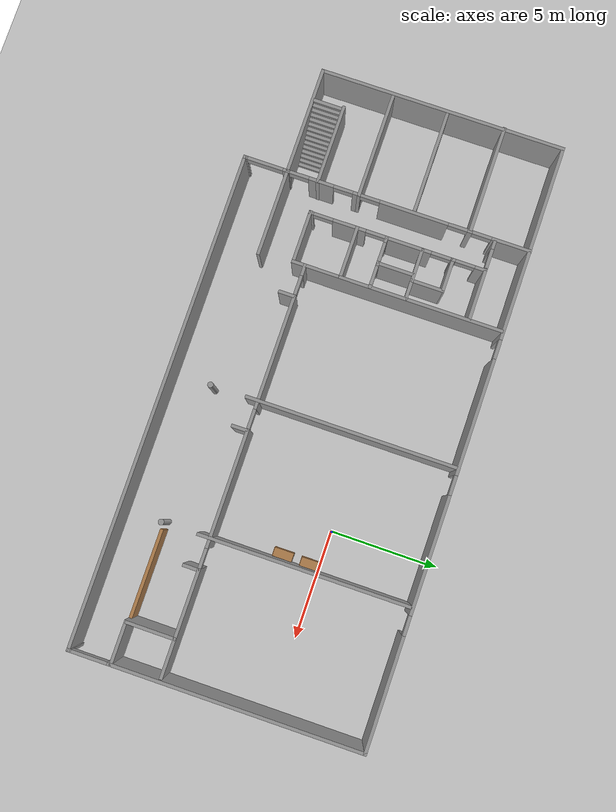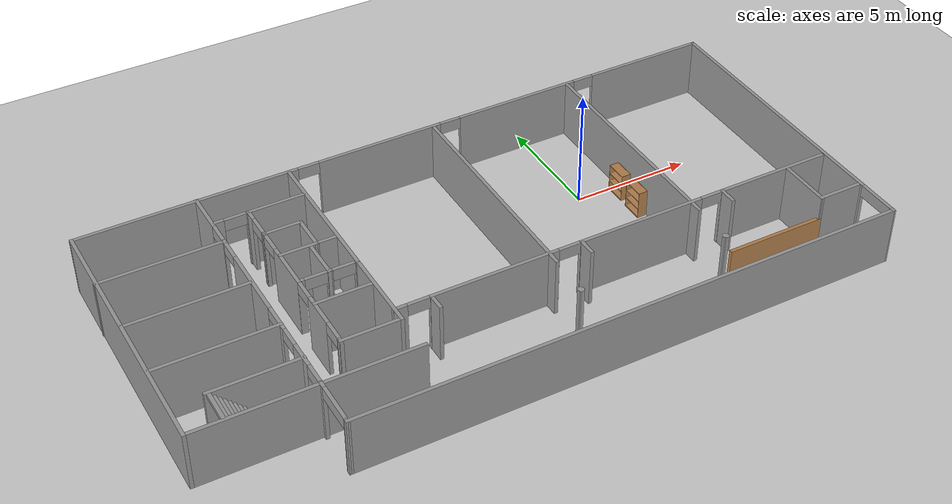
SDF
<sdf version="1.7">
 <world name="default">
  <light name="sun" type="directional">
   <pose>0 0 10 0 -0 0</pose>
   <diffuse>0.8 0.8 0.8 1</diffuse>
   <specular>0.2 0.2 0.2 1</specular>
   <attenuation>
    <range>1000</range>
    <constant>0.9</constant>
    <linear>0.01</linear>
    <quadratic>0.001</quadratic>
   </attenuation>
   <direction>-0.5 0.1 -0.9</direction>
   <spot><inner_angle>0</inner_angle><outer_angle>0</outer_angle><falloff>0</falloff></spot>
  </light>
  <model name="ground_plane">
   <static>1</static>
   <link name="link">
    <collision name="collision">
     <geometry><plane><normal>0 0 1</normal><size>100 100</size></plane></geometry>
     <surface><friction><ode><mu>100</mu><mu2>50</mu2></ode></friction></surface>
    </collision>
    <visual name="visual">
     <cast_shadows>0</cast_shadows>
     <geometry><plane><normal>0 0 1</normal><size>100 100</size></plane></geometry>
     <material>
      <script><uri>file://media/materials/scripts/gazebo.material</uri><name>Gazebo/Grey</name></script>
     </material>
    </visual>
   </link>
  </model>
  <gravity>0 0 -9.8</gravity>
  <magnetic_field>6e-06 2.3e-05 -4.2e-05</magnetic_field>
  <atmosphere type="adiabatic"/>
  <physics type="ode">
   <max_step_size>0.001</max_step_size>
   <real_time_factor>1</real_time_factor>
   <real_time_update_rate>1000</real_time_update_rate>
  </physics>
  <scene><ambient>0.4 0.4 0.4 1</ambient><background>0.7 0.7 0.7 1</background><shadows>1</shadows></scene>
  <spherical_coordinates>
   <surface_model>EARTH_WGS84</surface_model>
   <latitude_deg>0</latitude_deg>
   <longitude_deg>0</longitude_deg>
   <elevation>0</elevation>
   <heading_deg>0</heading_deg>
  </spherical_coordinates>
  <model name="batimentH">
   <link name="Stairs_1">
    <visual name="Stairs_1_Visual_0">
     <pose>-10.1559 -3.96803 0.083333 0 -0 -1.5708</pose>
     <geometry><box><size>1.32885 0.162742 0.166667</size></box></geometry>
     <material>
      <script><uri>file://media/materials/scripts/gazebo.material</uri><name>Gazebo/Grey</name></script>
      <ambient>1 1 1 1</ambient>
      <shader type="pixel"/>
     </material>
     <meta><layer>0</layer></meta>
    </visual>
    <visual name="Stairs_1_Visual_1">
     <pose>-10.3187 -3.96803 0.25 0 -0 -1.5708</pose>
     <geometry><box><size>1.32885 0.162742 0.166667</size></box></geometry>
     <material>
      <script><uri>file://media/materials/scripts/gazebo.material</uri><name>Gazebo/Grey</name></script>
      <ambient>1 1 1 1</ambient>
      <shader type="pixel"/>
     </material>
     <meta><layer>0</layer></meta>
    </visual>
    <visual name="Stairs_1_Visual_2">
     <pose>-10.4814 -3.96803 0.416667 0 -0 -1.5708</pose>
     <geometry><box><size>1.32885 0.162742 0.166667</size></box></geometry>
     <material>
      <script><uri>file://media/materials/scripts/gazebo.material</uri><name>Gazebo/Grey</name></script>
      <ambient>1 1 1 1</ambient>
      <shader type="pixel"/>
     </material>
     <meta><layer>0</layer></meta>
    </visual>
    <visual name="Stairs_1_Visual_3">
     <pose>-10.6442 -3.96803 0.583333 0 -0 -1.5708</pose>
     <geometry><box><size>1.32885 0.162742 0.166667</size></box></geometry>
     <material>
      <script><uri>file://media/materials/scripts/gazebo.material</uri><name>Gazebo/Grey</name></script>
      <ambient>1 1 1 1</ambient>
      <shader type="pixel"/>
     </material>
     <meta><layer>0</layer></meta>
    </visual>
    <visual name="Stairs_1_Visual_4">
     <pose>-10.8069 -3.96803 0.75 0 -0 -1.5708</pose>
     <geometry><box><size>1.32885 0.162742 0.166667</size></box></geometry>
     <material>
      <script><uri>file://media/materials/scripts/gazebo.material</uri><name>Gazebo/Grey</name></script>
      <ambient>1 1 1 1</ambient>
      <shader type="pixel"/>
     </material>
     <meta><layer>0</layer></meta>
    </visual>
    <visual name="Stairs_1_Visual_5">
     <pose>-10.9697 -3.96803 0.916667 0 -0 -1.5708</pose>
     <geometry><box><size>1.32885 0.162742 0.166667</size></box></geometry>
     <material>
      <script><uri>file://media/materials/scripts/gazebo.material</uri><name>Gazebo/Grey</name></script>
      <ambient>1 1 1 1</ambient>
      <shader type="pixel"/>
     </material>
     <meta><layer>0</layer></meta>
    </visual>
    <visual name="Stairs_1_Visual_6">
     <pose>-11.1324 -3.96803 1.08333 0 -0 -1.5708</pose>
     <geometry><box><size>1.32885 0.162742 0.166667</size></box></geometry>
     <material>
      <script><uri>file://media/materials/scripts/gazebo.material</uri><name>Gazebo/Grey</name></script>
      <ambient>1 1 1 1</ambient>
      <shader type="pixel"/>
     </material>
     <meta><layer>0</layer></meta>
    </visual>
    <visual name="Stairs_1_Visual_7">
     <pose>-11.2951 -3.96803 1.25 0 -0 -1.5708</pose>
     <geometry><box><size>1.32885 0.162742 0.166667</size></box></geometry>
     <material>
      <script><uri>file://media/materials/scripts/gazebo.material</uri><name>Gazebo/Grey</name></script>
      <ambient>1 1 1 1</ambient>
      <shader type="pixel"/>
     </material>
     <meta><layer>0</layer></meta>
    </visual>
    <visual name="Stairs_1_Visual_8">
     <pose>-11.4579 -3.96803 1.41667 0 -0 -1.5708</pose>
     <geometry><box><size>1.32885 0.162742 0.166667</size></box></geometry>
     <material>
      <script><uri>file://media/materials/scripts/gazebo.material</uri><name>Gazebo/Grey</name></script>
      <ambient>1 1 1 1</ambient>
      <shader type="pixel"/>
     </material>
     <meta><layer>0</layer></meta>
    </visual>
    <visual name="Stairs_1_Visual_9">
     <pose>-11.6206 -3.96803 1.58333 0 -0 -1.5708</pose>
     <geometry><box><size>1.32885 0.162742 0.166667</size></box></geometry>
     <material>
      <script><uri>file://media/materials/scripts/gazebo.material</uri><name>Gazebo/Grey</name></script>
      <ambient>1 1 1 1</ambient>
      <shader type="pixel"/>
     </material>
     <meta><layer>0</layer></meta>
    </visual>
    <visual name="Stairs_1_Visual_10">
     <pose>-11.7834 -3.96803 1.75 0 -0 -1.5708</pose>
     <geometry><box><size>1.32885 0.162742 0.166667</size></box></geometry>
     <material>
      <script><uri>file://media/materials/scripts/gazebo.material</uri><name>Gazebo/Grey</name></script>
      <ambient>1 1 1 1</ambient>
      <shader type="pixel"/>
     </material>
     <meta><layer>0</layer></meta>
    </visual>
    <visual name="Stairs_1_Visual_11">
     <pose>-11.9461 -3.96803 1.91667 0 -0 -1.5708</pose>
     <geometry><box><size>1.32885 0.162742 0.166667</size></box></geometry>
     <material>
      <script><uri>file://media/materials/scripts/gazebo.material</uri><name>Gazebo/Grey</name></script>
      <ambient>1 1 1 1</ambient>
      <shader type="pixel"/>
     </material>
     <meta><layer>0</layer></meta>
    </visual>
    <visual name="Stairs_1_Visual_12">
     <pose>-12.1089 -3.96803 2.08333 0 -0 -1.5708</pose>
     <geometry><box><size>1.32885 0.162742 0.166667</size></box></geometry>
     <material>
      <script><uri>file://media/materials/scripts/gazebo.material</uri><name>Gazebo/Grey</name></script>
      <ambient>1 1 1 1</ambient>
      <shader type="pixel"/>
     </material>
     <meta><layer>0</layer></meta>
    </visual>
    <visual name="Stairs_1_Visual_13">
     <pose>-12.2716 -3.96803 2.25 0 -0 -1.5708</pose>
     <geometry><box><size>1.32885 0.162742 0.166667</size></box></geometry>
     <material>
      <script><uri>file://media/materials/scripts/gazebo.material</uri><name>Gazebo/Grey</name></script>
      <ambient>1 1 1 1</ambient>
      <shader type="pixel"/>
     </material>
     <meta><layer>0</layer></meta>
    </visual>
    <visual name="Stairs_1_Visual_14">
     <pose>-12.4343 -3.96803 2.41667 0 -0 -1.5708</pose>
     <geometry><box><size>1.32885 0.162742 0.166667</size></box></geometry>
     <material>
      <script><uri>file://media/materials/scripts/gazebo.material</uri><name>Gazebo/Grey</name></script>
      <ambient>1 1 1 1</ambient>
      <shader type="pixel"/>
     </material>
     <meta><layer>0</layer></meta>
    </visual>
    <collision name="Stairs_1_Collision_0">
     <pose>-10.1559 -3.96803 0.083333 0 0 -1.5708</pose>
     <geometry><box><size>1.32885 0.162742 0.166667</size></box></geometry>
     <surface>
      <friction>
       <ode><mu>1</mu><mu2>1</mu2><fdir1>0 0 0</fdir1><slip1>0</slip1><slip2>0</slip2></ode>
       <torsional>
        <coefficient>1</coefficient>
        <patch_radius>0</patch_radius>
        <surface_radius>0</surface_radius>
        <use_patch_radius>1</use_patch_radius>
        <ode><slip>0</slip></ode>
       </torsional>
      </friction>
      <bounce><restitution_coefficient>0</restitution_coefficient><threshold>1e+06</threshold></bounce>
      <contact>
       <collide_without_contact>0</collide_without_contact>
       <collide_without_contact_bitmask>1</collide_without_contact_bitmask>
       <collide_bitmask>1</collide_bitmask>
       <ode>
        <soft_cfm>0</soft_cfm>
        <soft_erp>0.2</soft_erp>
        <kp>1e+13</kp>
        <kd>1</kd>
        <max_vel>0.01</max_vel>
        <min_depth>0</min_depth>
       </ode>
       <bullet>
        <split_impulse>1</split_impulse>
        <split_impulse_penetration_threshold>-0.01</split_impulse_penetration_threshold>
        <soft_cfm>0</soft_cfm>
        <soft_erp>0.2</soft_erp>
        <kp>1e+13</kp>
        <kd>1</kd>
       </bullet>
      </contact>
     </surface>
    </collision>
    <collision name="Stairs_1_Collision_1">
     <pose>-10.3187 -3.96803 0.25 0 0 -1.5708</pose>
     <geometry><box><size>1.32885 0.162742 0.166667</size></box></geometry>
     <surface>
      <friction>
       <ode><mu>1</mu><mu2>1</mu2><fdir1>0 0 0</fdir1><slip1>0</slip1><slip2>0</slip2></ode>
       <torsional>
        <coefficient>1</coefficient>
        <patch_radius>0</patch_radius>
        <surface_radius>0</surface_radius>
        <use_patch_radius>1</use_patch_radius>
        <ode><slip>0</slip></ode>
       </torsional>
      </friction>
      <bounce><restitution_coefficient>0</restitution_coefficient><threshold>1e+06</threshold></bounce>
      <contact>
       <collide_without_contact>0</collide_without_contact>
       <collide_without_contact_bitmask>1</collide_without_contact_bitmask>
       <collide_bitmask>1</collide_bitmask>
       <ode>
        <soft_cfm>0</soft_cfm>
        <soft_erp>0.2</soft_erp>
        <kp>1e+13</kp>
        <kd>1</kd>
        <max_vel>0.01</max_vel>
        <min_depth>0</min_depth>
       </ode>
       <bullet>
        <split_impulse>1</split_impulse>
        <split_impulse_penetration_threshold>-0.01</split_impulse_penetration_threshold>
        <soft_cfm>0</soft_cfm>
        <soft_erp>0.2</soft_erp>
        <kp>1e+13</kp>
        <kd>1</kd>
       </bullet>
      </contact>
     </surface>
    </collision>
    <collision name="Stairs_1_Collision_2">
     <pose>-10.4814 -3.96803 0.416667 0 0 -1.5708</pose>
     <geometry><box><size>1.32885 0.162742 0.166667</size></box></geometry>
     <surface>
      <friction>
       <ode><mu>1</mu><mu2>1</mu2><fdir1>0 0 0</fdir1><slip1>0</slip1><slip2>0</slip2></ode>
       <torsional>
        <coefficient>1</coefficient>
        <patch_radius>0</patch_radius>
        <surface_radius>0</surface_radius>
        <use_patch_radius>1</use_patch_radius>
        <ode><slip>0</slip></ode>
       </torsional>
      </friction>
      <bounce><restitution_coefficient>0</restitution_coefficient><threshold>1e+06</threshold></bounce>
      <contact>
       <collide_without_contact>0</collide_without_contact>
       <collide_without_contact_bitmask>1</collide_without_contact_bitmask>
       <collide_bitmask>1</collide_bitmask>
       <ode>
        <soft_cfm>0</soft_cfm>
        <soft_erp>0.2</soft_erp>
        <kp>1e+13</kp>
        <kd>1</kd>
        <max_vel>0.01</max_vel>
        <min_depth>0</min_depth>
       </ode>
       <bullet>
        <split_impulse>1</split_impulse>
        <split_impulse_penetration_threshold>-0.01</split_impulse_penetration_threshold>
        <soft_cfm>0</soft_cfm>
        <soft_erp>0.2</soft_erp>
        <kp>1e+13</kp>
        <kd>1</kd>
       </bullet>
      </contact>
     </surface>
    </collision>
    <collision name="Stairs_1_Collision_3">
     <pose>-10.6442 -3.96803 0.583333 0 0 -1.5708</pose>
     <geometry><box><size>1.32885 0.162742 0.166667</size></box></geometry>
     <surface>
      <friction>
       <ode><mu>1</mu><mu2>1</mu2><fdir1>0 0 0</fdir1><slip1>0</slip1><slip2>0</slip2></ode>
       <torsional>
        <coefficient>1</coefficient>
        <patch_radius>0</patch_radius>
        <surface_radius>0</surface_radius>
        <use_patch_radius>1</use_patch_radius>
        <ode><slip>0</slip></ode>
       </torsional>
      </friction>
      <bounce><restitution_coefficient>0</restitution_coefficient><threshold>1e+06</threshold></bounce>
      <contact>
       <collide_without_contact>0</collide_without_contact>
       <collide_without_contact_bitmask>1</collide_without_contact_bitmask>
       <collide_bitmask>1</collide_bitmask>
       <ode>
        <soft_cfm>0</soft_cfm>
        <soft_erp>0.2</soft_erp>
        <kp>1e+13</kp>
        <kd>1</kd>
        <max_vel>0.01</max_vel>
        <min_depth>0</min_depth>
       </ode>
       <bullet>
        <split_impulse>1</split_impulse>
        <split_impulse_penetration_threshold>-0.01</split_impulse_penetration_threshold>
        <soft_cfm>0</soft_cfm>
        <soft_erp>0.2</soft_erp>
        <kp>1e+13</kp>
        <kd>1</kd>
       </bullet>
      </contact>
     </surface>
    </collision>
    <collision name="Stairs_1_Collision_4">
     <pose>-10.8069 -3.96803 0.75 0 0 -1.5708</pose>
     <geometry><box><size>1.32885 0.162742 0.166667</size></box></geometry>
     <surface>
      <friction>
       <ode><mu>1</mu><mu2>1</mu2><fdir1>0 0 0</fdir1><slip1>0</slip1><slip2>0</slip2></ode>
       <torsional>
        <coefficient>1</coefficient>
        <patch_radius>0</patch_radius>
        <surface_radius>0</surface_radius>
        <use_patch_radius>1</use_patch_radius>
        <ode><slip>0</slip></ode>
       </torsional>
      </friction>
      <bounce><restitution_coefficient>0</restitution_coefficient><threshold>1e+06</threshold></bounce>
      <contact>
       <collide_without_contact>0</collide_without_contact>
       <collide_without_contact_bitmask>1</collide_without_contact_bitmask>
       <collide_bitmask>1</collide_bitmask>
       <ode>
        <soft_cfm>0</soft_cfm>
        <soft_erp>0.2</soft_erp>
        <kp>1e+13</kp>
        <kd>1</kd>
        <max_vel>0.01</max_vel>
        <min_depth>0</min_depth>
       </ode>
       <bullet>
        <split_impulse>1</split_impulse>
        <split_impulse_penetration_threshold>-0.01</split_impulse_penetration_threshold>
        <soft_cfm>0</soft_cfm>
        <soft_erp>0.2</soft_erp>
        <kp>1e+13</kp>
        <kd>1</kd>
       </bullet>
      </contact>
     </surface>
    </collision>
    <collision name="Stairs_1_Collision_5">
     <pose>-10.9697 -3.96803 0.916667 0 0 -1.5708</pose>
     <geometry><box><size>1.32885 0.162742 0.166667</size></box></geometry>
     <surface>
      <friction>
       <ode><mu>1</mu><mu2>1</mu2><fdir1>0 0 0</fdir1><slip1>0</slip1><slip2>0</slip2></ode>
       <torsional>
        <coefficient>1</coefficient>
        <patch_radius>0</patch_radius>
        <surface_radius>0</surface_radius>
        <use_patch_radius>1</use_patch_radius>
        <ode><slip>0</slip></ode>
       </torsional>
      </friction>
      <bounce><restitution_coefficient>0</restitution_coefficient><threshold>1e+06</threshold></bounce>
      <contact>
       <collide_without_contact>0</collide_without_contact>
       <collide_without_contact_bitmask>1</collide_without_contact_bitmask>
       <collide_bitmask>1</collide_bitmask>
       <ode>
        <soft_cfm>0</soft_cfm>
        <soft_erp>0.2</soft_erp>
        <kp>1e+13</kp>
        <kd>1</kd>
        <max_vel>0.01</max_vel>
        <min_depth>0</min_depth>
       </ode>
       <bullet>
        <split_impulse>1</split_impulse>
        <split_impulse_penetration_threshold>-0.01</split_impulse_penetration_threshold>
        <soft_cfm>0</soft_cfm>
        <soft_erp>0.2</soft_erp>
        <kp>1e+13</kp>
        <kd>1</kd>
       </bullet>
      </contact>
     </surface>
    </collision>
    <collision name="Stairs_1_Collision_6">
     <pose>-11.1324 -3.96803 1.08333 0 0 -1.5708</pose>
     <geometry><box><size>1.32885 0.162742 0.166667</size></box></geometry>
     <surface>
      <friction>
       <ode><mu>1</mu><mu2>1</mu2><fdir1>0 0 0</fdir1><slip1>0</slip1><slip2>0</slip2></ode>
       <torsional>
        <coefficient>1</coefficient>
        <patch_radius>0</patch_radius>
        <surface_radius>0</surface_radius>
        <use_patch_radius>1</use_patch_radius>
        <ode><slip>0</slip></ode>
       </torsional>
      </friction>
      <bounce><restitution_coefficient>0</restitution_coefficient><threshold>1e+06</threshold></bounce>
      <contact>
       <collide_without_contact>0</collide_without_contact>
       <collide_without_contact_bitmask>1</collide_without_contact_bitmask>
       <collide_bitmask>1</collide_bitmask>
       <ode>
        <soft_cfm>0</soft_cfm>
        <soft_erp>0.2</soft_erp>
        <kp>1e+13</kp>
        <kd>1</kd>
        <max_vel>0.01</max_vel>
        <min_depth>0</min_depth>
       </ode>
       <bullet>
        <split_impulse>1</split_impulse>
        <split_impulse_penetration_threshold>-0.01</split_impulse_penetration_threshold>
        <soft_cfm>0</soft_cfm>
        <soft_erp>0.2</soft_erp>
        <kp>1e+13</kp>
        <kd>1</kd>
       </bullet>
      </contact>
     </surface>
    </collision>
    <collision name="Stairs_1_Collision_7">
     <pose>-11.2951 -3.96803 1.25 0 0 -1.5708</pose>
     <geometry><box><size>1.32885 0.162742 0.166667</size></box></geometry>
     <surface>
      <friction>
       <ode><mu>1</mu><mu2>1</mu2><fdir1>0 0 0</fdir1><slip1>0</slip1><slip2>0</slip2></ode>
       <torsional>
        <coefficient>1</coefficient>
        <patch_radius>0</patch_radius>
        <surface_radius>0</surface_radius>
        <use_patch_radius>1</use_patch_radius>
        <ode><slip>0</slip></ode>
       </torsional>
      </friction>
      <bounce><restitution_coefficient>0</restitution_coefficient><threshold>1e+06</threshold></bounce>
      <contact>
       <collide_without_contact>0</collide_without_contact>
       <collide_without_contact_bitmask>1</collide_without_contact_bitmask>
       <collide_bitmask>1</collide_bitmask>
       <ode>
        <soft_cfm>0</soft_cfm>
        <soft_erp>0.2</soft_erp>
        <kp>1e+13</kp>
        <kd>1</kd>
        <max_vel>0.01</max_vel>
        <min_depth>0</min_depth>
       </ode>
       <bullet>
        <split_impulse>1</split_impulse>
        <split_impulse_penetration_threshold>-0.01</split_impulse_penetration_threshold>
        <soft_cfm>0</soft_cfm>
        <soft_erp>0.2</soft_erp>
        <kp>1e+13</kp>
        <kd>1</kd>
       </bullet>
      </contact>
     </surface>
    </collision>
    <collision name="Stairs_1_Collision_8">
     <pose>-11.4579 -3.96803 1.41667 0 0 -1.5708</pose>
     <geometry><box><size>1.32885 0.162742 0.166667</size></box></geometry>
     <surface>
      <friction>
       <ode><mu>1</mu><mu2>1</mu2><fdir1>0 0 0</fdir1><slip1>0</slip1><slip2>0</slip2></ode>
       <torsional>
        <coefficient>1</coefficient>
        <patch_radius>0</patch_radius>
        <surface_radius>0</surface_radius>
        <use_patch_radius>1</use_patch_radius>
        <ode><slip>0</slip></ode>
       </torsional>
      </friction>
      <bounce><restitution_coefficient>0</restitution_coefficient><threshold>1e+06</threshold></bounce>
      <contact>
       <collide_without_contact>0</collide_without_contact>
       <collide_without_contact_bitmask>1</collide_without_contact_bitmask>
       <collide_bitmask>1</collide_bitmask>
       <ode>
        <soft_cfm>0</soft_cfm>
        <soft_erp>0.2</soft_erp>
        <kp>1e+13</kp>
        <kd>1</kd>
        <max_vel>0.01</max_vel>
        <min_depth>0</min_depth>
       </ode>
       <bullet>
        <split_impulse>1</split_impulse>
        <split_impulse_penetration_threshold>-0.01</split_impulse_penetration_threshold>
        <soft_cfm>0</soft_cfm>
        <soft_erp>0.2</soft_erp>
        <kp>1e+13</kp>
        <kd>1</kd>
       </bullet>
      </contact>
     </surface>
    </collision>
    <collision name="Stairs_1_Collision_10">
     <pose>-11.7834 -3.96803 1.75 0 0 -1.5708</pose>
     <geometry><box><size>1.32885 0.162742 0.166667</size></box></geometry>
     <surface>
      <friction>
       <ode><mu>1</mu><mu2>1</mu2><fdir1>0 0 0</fdir1><slip1>0</slip1><slip2>0</slip2></ode>
       <torsional>
        <coefficient>1</coefficient>
        <patch_radius>0</patch_radius>
        <surface_radius>0</surface_radius>
        <use_patch_radius>1</use_patch_radius>
        <ode><slip>0</slip></ode>
       </torsional>
      </friction>
      <bounce><restitution_coefficient>0</restitution_coefficient><threshold>1e+06</threshold></bounce>
      <contact>
       <collide_without_contact>0</collide_without_contact>
       <collide_without_contact_bitmask>1</collide_without_contact_bitmask>
       <collide_bitmask>1</collide_bitmask>
       <ode>
        <soft_cfm>0</soft_cfm>
        <soft_erp>0.2</soft_erp>
        <kp>1e+13</kp>
        <kd>1</kd>
        <max_vel>0.01</max_vel>
        <min_depth>0</min_depth>
       </ode>
       <bullet>
        <split_impulse>1</split_impulse>
        <split_impulse_penetration_threshold>-0.01</split_impulse_penetration_threshold>
        <soft_cfm>0</soft_cfm>
        <soft_erp>0.2</soft_erp>
        <kp>1e+13</kp>
        <kd>1</kd>
       </bullet>
      </contact>
     </surface>
    </collision>
    <collision name="Stairs_1_Collision_9">
     <pose>-11.6206 -3.96803 1.58333 0 0 -1.5708</pose>
     <geometry><box><size>1.32885 0.162742 0.166667</size></box></geometry>
     <surface>
      <friction>
       <ode><mu>1</mu><mu2>1</mu2><fdir1>0 0 0</fdir1><slip1>0</slip1><slip2>0</slip2></ode>
       <torsional>
        <coefficient>1</coefficient>
        <patch_radius>0</patch_radius>
        <surface_radius>0</surface_radius>
        <use_patch_radius>1</use_patch_radius>
        <ode><slip>0</slip></ode>
       </torsional>
      </friction>
      <bounce><restitution_coefficient>0</restitution_coefficient><threshold>1e+06</threshold></bounce>
      <contact>
       <collide_without_contact>0</collide_without_contact>
       <collide_without_contact_bitmask>1</collide_without_contact_bitmask>
       <collide_bitmask>1</collide_bitmask>
       <ode>
        <soft_cfm>0</soft_cfm>
        <soft_erp>0.2</soft_erp>
        <kp>1e+13</kp>
        <kd>1</kd>
        <max_vel>0.01</max_vel>
        <min_depth>0</min_depth>
       </ode>
       <bullet>
        <split_impulse>1</split_impulse>
        <split_impulse_penetration_threshold>-0.01</split_impulse_penetration_threshold>
        <soft_cfm>0</soft_cfm>
        <soft_erp>0.2</soft_erp>
        <kp>1e+13</kp>
        <kd>1</kd>
       </bullet>
      </contact>
     </surface>
    </collision>
    <collision name="Stairs_1_Collision_11">
     <pose>-11.9461 -3.96803 1.91667 0 0 -1.5708</pose>
     <geometry><box><size>1.32885 0.162742 0.166667</size></box></geometry>
     <surface>
      <friction>
       <ode><mu>1</mu><mu2>1</mu2><fdir1>0 0 0</fdir1><slip1>0</slip1><slip2>0</slip2></ode>
       <torsional>
        <coefficient>1</coefficient>
        <patch_radius>0</patch_radius>
        <surface_radius>0</surface_radius>
        <use_patch_radius>1</use_patch_radius>
        <ode><slip>0</slip></ode>
       </torsional>
      </friction>
      <bounce><restitution_coefficient>0</restitution_coefficient><threshold>1e+06</threshold></bounce>
      <contact>
       <collide_without_contact>0</collide_without_contact>
       <collide_without_contact_bitmask>1</collide_without_contact_bitmask>
       <collide_bitmask>1</collide_bitmask>
       <ode>
        <soft_cfm>0</soft_cfm>
        <soft_erp>0.2</soft_erp>
        <kp>1e+13</kp>
        <kd>1</kd>
        <max_vel>0.01</max_vel>
        <min_depth>0</min_depth>
       </ode>
       <bullet>
        <split_impulse>1</split_impulse>
        <split_impulse_penetration_threshold>-0.01</split_impulse_penetration_threshold>
        <soft_cfm>0</soft_cfm>
        <soft_erp>0.2</soft_erp>
        <kp>1e+13</kp>
        <kd>1</kd>
       </bullet>
      </contact>
     </surface>
    </collision>
    <collision name="Stairs_1_Collision_12">
     <pose>-12.1089 -3.96803 2.08333 0 0 -1.5708</pose>
     <geometry><box><size>1.32885 0.162742 0.166667</size></box></geometry>
     <surface>
      <friction>
       <ode><mu>1</mu><mu2>1</mu2><fdir1>0 0 0</fdir1><slip1>0</slip1><slip2>0</slip2></ode>
       <torsional>
        <coefficient>1</coefficient>
        <patch_radius>0</patch_radius>
        <surface_radius>0</surface_radius>
        <use_patch_radius>1</use_patch_radius>
        <ode><slip>0</slip></ode>
       </torsional>
      </friction>
      <bounce><restitution_coefficient>0</restitution_coefficient><threshold>1e+06</threshold></bounce>
      <contact>
       <collide_without_contact>0</collide_without_contact>
       <collide_without_contact_bitmask>1</collide_without_contact_bitmask>
       <collide_bitmask>1</collide_bitmask>
       <ode>
        <soft_cfm>0</soft_cfm>
        <soft_erp>0.2</soft_erp>
        <kp>1e+13</kp>
        <kd>1</kd>
        <max_vel>0.01</max_vel>
        <min_depth>0</min_depth>
       </ode>
       <bullet>
        <split_impulse>1</split_impulse>
        <split_impulse_penetration_threshold>-0.01</split_impulse_penetration_threshold>
        <soft_cfm>0</soft_cfm>
        <soft_erp>0.2</soft_erp>
        <kp>1e+13</kp>
        <kd>1</kd>
       </bullet>
      </contact>
     </surface>
    </collision>
    <collision name="Stairs_1_Collision_13">
     <pose>-12.2716 -3.96803 2.25 0 0 -1.5708</pose>
     <geometry><box><size>1.32885 0.162742 0.166667</size></box></geometry>
     <surface>
      <friction>
       <ode><mu>1</mu><mu2>1</mu2><fdir1>0 0 0</fdir1><slip1>0</slip1><slip2>0</slip2></ode>
       <torsional>
        <coefficient>1</coefficient>
        <patch_radius>0</patch_radius>
        <surface_radius>0</surface_radius>
        <use_patch_radius>1</use_patch_radius>
        <ode><slip>0</slip></ode>
       </torsional>
      </friction>
      <bounce><restitution_coefficient>0</restitution_coefficient><threshold>1e+06</threshold></bounce>
      <contact>
       <collide_without_contact>0</collide_without_contact>
       <collide_without_contact_bitmask>1</collide_without_contact_bitmask>
       <collide_bitmask>1</collide_bitmask>
       <ode>
        <soft_cfm>0</soft_cfm>
        <soft_erp>0.2</soft_erp>
        <kp>1e+13</kp>
        <kd>1</kd>
        <max_vel>0.01</max_vel>
        <min_depth>0</min_depth>
       </ode>
       <bullet>
        <split_impulse>1</split_impulse>
        <split_impulse_penetration_threshold>-0.01</split_impulse_penetration_threshold>
        <soft_cfm>0</soft_cfm>
        <soft_erp>0.2</soft_erp>
        <kp>1e+13</kp>
        <kd>1</kd>
       </bullet>
      </contact>
     </surface>
    </collision>
    <collision name="Stairs_1_Collision_14">
     <pose>-12.4343 -3.96803 2.41667 0 0 -1.5708</pose>
     <geometry><box><size>1.32885 0.162742 0.166667</size></box></geometry>
     <surface>
      <friction>
       <ode><mu>1</mu><mu2>1</mu2><fdir1>0 0 0</fdir1><slip1>0</slip1><slip2>0</slip2></ode>
       <torsional>
        <coefficient>1</coefficient>
        <patch_radius>0</patch_radius>
        <surface_radius>0</surface_radius>
        <use_patch_radius>1</use_patch_radius>
        <ode><slip>0</slip></ode>
       </torsional>
      </friction>
      <bounce><restitution_coefficient>0</restitution_coefficient><threshold>1e+06</threshold></bounce>
      <contact>
       <collide_without_contact>0</collide_without_contact>
       <collide_without_contact_bitmask>1</collide_without_contact_bitmask>
       <collide_bitmask>1</collide_bitmask>
       <ode>
        <soft_cfm>0</soft_cfm>
        <soft_erp>0.2</soft_erp>
        <kp>1e+13</kp>
        <kd>1</kd>
        <max_vel>0.01</max_vel>
        <min_depth>0</min_depth>
       </ode>
       <bullet>
        <split_impulse>1</split_impulse>
        <split_impulse_penetration_threshold>-0.01</split_impulse_penetration_threshold>
        <soft_cfm>0</soft_cfm>
        <soft_erp>0.2</soft_erp>
        <kp>1e+13</kp>
        <kd>1</kd>
       </bullet>
      </contact>
     </surface>
    </collision>
   </link>
   <link name="Wall_0">
    <pose>0.006105 6.66605 0 0 -0 3.1407</pose>
    <visual name="Wall_0_Visual_0">
     <pose>-11.3504 0 1.25 0 -0 0</pose>
     <geometry><box><size>5.217 0.15 2.5</size></box></geometry>
     <material>
      <script><uri>file://media/materials/scripts/gazebo.material</uri><name>Gazebo/Grey</name></script>
      <ambient>1 1 1 1</ambient>
      <shader type="pixel"/>
     </material>
     <meta><layer>0</layer></meta>
    </visual>
    <visual name="Wall_0_Visual_1">
     <pose>-5.13636 0 1.25 0 -0 0</pose>
     <geometry><box><size>5.41105 0.15 2.5</size></box></geometry>
     <material>
      <script><uri>file://media/materials/scripts/gazebo.material</uri><name>Gazebo/Grey</name></script>
      <ambient>1 1 1 1</ambient>
      <shader type="pixel"/>
     </material>
     <meta><layer>0</layer></meta>
    </visual>
    <visual name="Wall_0_Visual_2">
     <pose>1.1607 0 1.25 0 -0 0</pose>
     <geometry><box><size>5.38305 0.15 2.5</size></box></geometry>
     <material>
      <script><uri>file://media/materials/scripts/gazebo.material</uri><name>Gazebo/Grey</name></script>
      <ambient>1 1 1 1</ambient>
      <shader type="pixel"/>
     </material>
     <meta><layer>0</layer></meta>
    </visual>
    <visual name="Wall_0_Visual_3">
     <pose>9.35555 0 1.25 0 -0 0</pose>
     <geometry><box><size>9.20665 0.15 2.5</size></box></geometry>
     <material>
      <script><uri>file://media/materials/scripts/gazebo.material</uri><name>Gazebo/Grey</name></script>
      <ambient>1 1 1 1</ambient>
      <shader type="pixel"/>
     </material>
     <meta><layer>0</layer></meta>
    </visual>
    <visual name="Wall_0_Visual_4">
     <pose>-8.29188 0 2.25 0 -0 0</pose>
     <geometry><box><size>0.9 0.15 0.5</size></box></geometry>
     <material>
      <script><uri>file://media/materials/scripts/gazebo.material</uri><name>Gazebo/Grey</name></script>
      <ambient>1 1 1 1</ambient>
      <shader type="pixel"/>
     </material>
     <meta><layer>0</layer></meta>
    </visual>
    <visual name="Wall_0_Visual_5">
     <pose>-1.98083 0 2.25 0 -0 0</pose>
     <geometry><box><size>0.9 0.15 0.5</size></box></geometry>
     <material>
      <script><uri>file://media/materials/scripts/gazebo.material</uri><name>Gazebo/Grey</name></script>
      <ambient>1 1 1 1</ambient>
      <shader type="pixel"/>
     </material>
     <meta><layer>0</layer></meta>
    </visual>
    <visual name="Wall_0_Visual_6">
     <pose>4.30223 0 2.25 0 -0 0</pose>
     <geometry><box><size>0.9 0.15 0.5</size></box></geometry>
     <material>
      <script><uri>file://media/materials/scripts/gazebo.material</uri><name>Gazebo/Grey</name></script>
      <ambient>1 1 1 1</ambient>
      <shader type="pixel"/>
     </material>
     <meta><layer>0</layer></meta>
    </visual>
    <collision name="Wall_0_Collision_0">
     <pose>-11.3504 0 1.25 0 -0 0</pose>
     <geometry><box><size>5.217 0.15 2.5</size></box></geometry>
     <surface>
      <friction>
       <ode><mu>1</mu><mu2>1</mu2><fdir1>0 0 0</fdir1><slip1>0</slip1><slip2>0</slip2></ode>
       <torsional>
        <coefficient>1</coefficient>
        <patch_radius>0</patch_radius>
        <surface_radius>0</surface_radius>
        <use_patch_radius>1</use_patch_radius>
        <ode><slip>0</slip></ode>
       </torsional>
      </friction>
      <bounce><restitution_coefficient>0</restitution_coefficient><threshold>1e+06</threshold></bounce>
      <contact>
       <collide_without_contact>0</collide_without_contact>
       <collide_without_contact_bitmask>1</collide_without_contact_bitmask>
       <collide_bitmask>1</collide_bitmask>
       <ode>
        <soft_cfm>0</soft_cfm>
        <soft_erp>0.2</soft_erp>
        <kp>1e+13</kp>
        <kd>1</kd>
        <max_vel>0.01</max_vel>
        <min_depth>0</min_depth>
       </ode>
       <bullet>
        <split_impulse>1</split_impulse>
        <split_impulse_penetration_threshold>-0.01</split_impulse_penetration_threshold>
        <soft_cfm>0</soft_cfm>
        <soft_erp>0.2</soft_erp>
        <kp>1e+13</kp>
        <kd>1</kd>
       </bullet>
      </contact>
     </surface>
    </collision>
    <collision name="Wall_0_Collision_1">
     <pose>-5.13636 0 1.25 0 -0 0</pose>
     <geometry><box><size>5.41105 0.15 2.5</size></box></geometry>
     <surface>
      <friction>
       <ode><mu>1</mu><mu2>1</mu2><fdir1>0 0 0</fdir1><slip1>0</slip1><slip2>0</slip2></ode>
       <torsional>
        <coefficient>1</coefficient>
        <patch_radius>0</patch_radius>
        <surface_radius>0</surface_radius>
        <use_patch_radius>1</use_patch_radius>
        <ode><slip>0</slip></ode>
       </torsional>
      </friction>
      <bounce><restitution_coefficient>0</restitution_coefficient><threshold>1e+06</threshold></bounce>
      <contact>
       <collide_without_contact>0</collide_without_contact>
       <collide_without_contact_bitmask>1</collide_without_contact_bitmask>
       <collide_bitmask>1</collide_bitmask>
       <ode>
        <soft_cfm>0</soft_cfm>
        <soft_erp>0.2</soft_erp>
        <kp>1e+13</kp>
        <kd>1</kd>
        <max_vel>0.01</max_vel>
        <min_depth>0</min_depth>
       </ode>
       <bullet>
        <split_impulse>1</split_impulse>
        <split_impulse_penetration_threshold>-0.01</split_impulse_penetration_threshold>
        <soft_cfm>0</soft_cfm>
        <soft_erp>0.2</soft_erp>
        <kp>1e+13</kp>
        <kd>1</kd>
       </bullet>
      </contact>
     </surface>
    </collision>
    <collision name="Wall_0_Collision_2">
     <pose>1.1607 0 1.25 0 -0 0</pose>
     <geometry><box><size>5.38305 0.15 2.5</size></box></geometry>
     <surface>
      <friction>
       <ode><mu>1</mu><mu2>1</mu2><fdir1>0 0 0</fdir1><slip1>0</slip1><slip2>0</slip2></ode>
       <torsional>
        <coefficient>1</coefficient>
        <patch_radius>0</patch_radius>
        <surface_radius>0</surface_radius>
        <use_patch_radius>1</use_patch_radius>
        <ode><slip>0</slip></ode>
       </torsional>
      </friction>
      <bounce><restitution_coefficient>0</restitution_coefficient><threshold>1e+06</threshold></bounce>
      <contact>
       <collide_without_contact>0</collide_without_contact>
       <collide_without_contact_bitmask>1</collide_without_contact_bitmask>
       <collide_bitmask>1</collide_bitmask>
       <ode>
        <soft_cfm>0</soft_cfm>
        <soft_erp>0.2</soft_erp>
        <kp>1e+13</kp>
        <kd>1</kd>
        <max_vel>0.01</max_vel>
        <min_depth>0</min_depth>
       </ode>
       <bullet>
        <split_impulse>1</split_impulse>
        <split_impulse_penetration_threshold>-0.01</split_impulse_penetration_threshold>
        <soft_cfm>0</soft_cfm>
        <soft_erp>0.2</soft_erp>
        <kp>1e+13</kp>
        <kd>1</kd>
       </bullet>
      </contact>
     </surface>
    </collision>
    <collision name="Wall_0_Collision_3">
     <pose>9.35555 0 1.25 0 -0 0</pose>
     <geometry><box><size>9.20665 0.15 2.5</size></box></geometry>
     <surface>
      <friction>
       <ode><mu>1</mu><mu2>1</mu2><fdir1>0 0 0</fdir1><slip1>0</slip1><slip2>0</slip2></ode>
       <torsional>
        <coefficient>1</coefficient>
        <patch_radius>0</patch_radius>
        <surface_radius>0</surface_radius>
        <use_patch_radius>1</use_patch_radius>
        <ode><slip>0</slip></ode>
       </torsional>
      </friction>
      <bounce><restitution_coefficient>0</restitution_coefficient><threshold>1e+06</threshold></bounce>
      <contact>
       <collide_without_contact>0</collide_without_contact>
       <collide_without_contact_bitmask>1</collide_without_contact_bitmask>
       <collide_bitmask>1</collide_bitmask>
       <ode>
        <soft_cfm>0</soft_cfm>
        <soft_erp>0.2</soft_erp>
        <kp>1e+13</kp>
        <kd>1</kd>
        <max_vel>0.01</max_vel>
        <min_depth>0</min_depth>
       </ode>
       <bullet>
        <split_impulse>1</split_impulse>
        <split_impulse_penetration_threshold>-0.01</split_impulse_penetration_threshold>
        <soft_cfm>0</soft_cfm>
        <soft_erp>0.2</soft_erp>
        <kp>1e+13</kp>
        <kd>1</kd>
       </bullet>
      </contact>
     </surface>
    </collision>
    <collision name="Wall_0_Collision_4">
     <pose>-8.29188 0 2.25 0 -0 0</pose>
     <geometry><box><size>0.9 0.15 0.5</size></box></geometry>
     <surface>
      <friction>
       <ode><mu>1</mu><mu2>1</mu2><fdir1>0 0 0</fdir1><slip1>0</slip1><slip2>0</slip2></ode>
       <torsional>
        <coefficient>1</coefficient>
        <patch_radius>0</patch_radius>
        <surface_radius>0</surface_radius>
        <use_patch_radius>1</use_patch_radius>
        <ode><slip>0</slip></ode>
       </torsional>
      </friction>
      <bounce><restitution_coefficient>0</restitution_coefficient><threshold>1e+06</threshold></bounce>
      <contact>
       <collide_without_contact>0</collide_without_contact>
       <collide_without_contact_bitmask>1</collide_without_contact_bitmask>
       <collide_bitmask>1</collide_bitmask>
       <ode>
        <soft_cfm>0</soft_cfm>
        <soft_erp>0.2</soft_erp>
        <kp>1e+13</kp>
        <kd>1</kd>
        <max_vel>0.01</max_vel>
        <min_depth>0</min_depth>
       </ode>
       <bullet>
        <split_impulse>1</split_impulse>
        <split_impulse_penetration_threshold>-0.01</split_impulse_penetration_threshold>
        <soft_cfm>0</soft_cfm>
        <soft_erp>0.2</soft_erp>
        <kp>1e+13</kp>
        <kd>1</kd>
       </bullet>
      </contact>
     </surface>
    </collision>
    <collision name="Wall_0_Collision_5">
     <pose>-1.98083 0 2.25 0 -0 0</pose>
     <geometry><box><size>0.9 0.15 0.5</size></box></geometry>
     <surface>
      <friction>
       <ode><mu>1</mu><mu2>1</mu2><fdir1>0 0 0</fdir1><slip1>0</slip1><slip2>0</slip2></ode>
       <torsional>
        <coefficient>1</coefficient>
        <patch_radius>0</patch_radius>
        <surface_radius>0</surface_radius>
        <use_patch_radius>1</use_patch_radius>
        <ode><slip>0</slip></ode>
       </torsional>
      </friction>
      <bounce><restitution_coefficient>0</restitution_coefficient><threshold>1e+06</threshold></bounce>
      <contact>
       <collide_without_contact>0</collide_without_contact>
       <collide_without_contact_bitmask>1</collide_without_contact_bitmask>
       <collide_bitmask>1</collide_bitmask>
       <ode>
        <soft_cfm>0</soft_cfm>
        <soft_erp>0.2</soft_erp>
        <kp>1e+13</kp>
        <kd>1</kd>
        <max_vel>0.01</max_vel>
        <min_depth>0</min_depth>
       </ode>
       <bullet>
        <split_impulse>1</split_impulse>
        <split_impulse_penetration_threshold>-0.01</split_impulse_penetration_threshold>
        <soft_cfm>0</soft_cfm>
        <soft_erp>0.2</soft_erp>
        <kp>1e+13</kp>
        <kd>1</kd>
       </bullet>
      </contact>
     </surface>
    </collision>
    <collision name="Wall_0_Collision_6">
     <pose>4.30223 0 2.25 0 -0 0</pose>
     <geometry><box><size>0.9 0.15 0.5</size></box></geometry>
     <surface>
      <friction>
       <ode><mu>1</mu><mu2>1</mu2><fdir1>0 0 0</fdir1><slip1>0</slip1><slip2>0</slip2></ode>
       <torsional>
        <coefficient>1</coefficient>
        <patch_radius>0</patch_radius>
        <surface_radius>0</surface_radius>
        <use_patch_radius>1</use_patch_radius>
        <ode><slip>0</slip></ode>
       </torsional>
      </friction>
      <bounce><restitution_coefficient>0</restitution_coefficient><threshold>1e+06</threshold></bounce>
      <contact>
       <collide_without_contact>0</collide_without_contact>
       <collide_without_contact_bitmask>1</collide_without_contact_bitmask>
       <collide_bitmask>1</collide_bitmask>
       <ode>
        <soft_cfm>0</soft_cfm>
        <soft_erp>0.2</soft_erp>
        <kp>1e+13</kp>
        <kd>1</kd>
        <max_vel>0.01</max_vel>
        <min_depth>0</min_depth>
       </ode>
       <bullet>
        <split_impulse>1</split_impulse>
        <split_impulse_penetration_threshold>-0.01</split_impulse_penetration_threshold>
        <soft_cfm>0</soft_cfm>
        <soft_erp>0.2</soft_erp>
        <kp>1e+13</kp>
        <kd>1</kd>
       </bullet>
      </contact>
     </surface>
    </collision>
   </link>
   <link name="Wall_1">
    <pose>-13.8701 1.00339 0 0 0 -1.56945</pose>
    <visual name="Wall_1_Visual">
     <pose>0 0 1.25 0 -0 0</pose>
     <geometry><box><size>11.5003 0.15 2.5</size></box></geometry>
     <material>
      <script><uri>file://media/materials/scripts/gazebo.material</uri><name>Gazebo/Grey</name></script>
      <ambient>1 1 1 1</ambient>
      <shader type="pixel"/>
     </material>
     <meta><layer>0</layer></meta>
    </visual>
    <collision name="Wall_1_Collision">
     <pose>0 0 1.25 0 -0 0</pose>
     <geometry><box><size>11.5003 0.15 2.5</size></box></geometry>
     <surface>
      <friction>
       <ode><mu>1</mu><mu2>1</mu2><fdir1>0 0 0</fdir1><slip1>0</slip1><slip2>0</slip2></ode>
       <torsional>
        <coefficient>1</coefficient>
        <patch_radius>0</patch_radius>
        <surface_radius>0</surface_radius>
        <use_patch_radius>1</use_patch_radius>
        <ode><slip>0</slip></ode>
       </torsional>
      </friction>
      <bounce><restitution_coefficient>0</restitution_coefficient><threshold>1e+06</threshold></bounce>
      <contact>
       <collide_without_contact>0</collide_without_contact>
       <collide_without_contact_bitmask>1</collide_without_contact_bitmask>
       <collide_bitmask>1</collide_bitmask>
       <ode>
        <soft_cfm>0</soft_cfm>
        <soft_erp>0.2</soft_erp>
        <kp>1e+13</kp>
        <kd>1</kd>
        <max_vel>0.01</max_vel>
        <min_depth>0</min_depth>
       </ode>
       <bullet>
        <split_impulse>1</split_impulse>
        <split_impulse_penetration_threshold>-0.01</split_impulse_penetration_threshold>
        <soft_cfm>0</soft_cfm>
        <soft_erp>0.2</soft_erp>
        <kp>1e+13</kp>
        <kd>1</kd>
       </bullet>
      </contact>
     </surface>
    </collision>
   </link>
   <link name="Wall_10">
    <pose>-11.4774 3.90885 0 0 -0 0</pose>
    <visual name="Wall_10_Visual">
     <pose>0 0 1.25 0 -0 0</pose>
     <geometry><box><size>5 0.15 2.5</size></box></geometry>
     <material>
      <script><uri>file://media/materials/scripts/gazebo.material</uri><name>Gazebo/Grey</name></script>
      <ambient>1 1 1 1</ambient>
      <shader type="pixel"/>
     </material>
     <meta><layer>0</layer></meta>
    </visual>
    <collision name="Wall_10_Collision">
     <pose>0 0 1.25 0 -0 0</pose>
     <geometry><box><size>5 0.15 2.5</size></box></geometry>
     <surface>
      <friction>
       <ode><mu>1</mu><mu2>1</mu2><fdir1>0 0 0</fdir1><slip1>0</slip1><slip2>0</slip2></ode>
       <torsional>
        <coefficient>1</coefficient>
        <patch_radius>0</patch_radius>
        <surface_radius>0</surface_radius>
        <use_patch_radius>1</use_patch_radius>
        <ode><slip>0</slip></ode>
       </torsional>
      </friction>
      <bounce><restitution_coefficient>0</restitution_coefficient><threshold>1e+06</threshold></bounce>
      <contact>
       <collide_without_contact>0</collide_without_contact>
       <collide_without_contact_bitmask>1</collide_without_contact_bitmask>
       <collide_bitmask>1</collide_bitmask>
       <ode>
        <soft_cfm>0</soft_cfm>
        <soft_erp>0.2</soft_erp>
        <kp>1e+13</kp>
        <kd>1</kd>
        <max_vel>0.01</max_vel>
        <min_depth>0</min_depth>
       </ode>
       <bullet>
        <split_impulse>1</split_impulse>
        <split_impulse_penetration_threshold>-0.01</split_impulse_penetration_threshold>
        <soft_cfm>0</soft_cfm>
        <soft_erp>0.2</soft_erp>
        <kp>1e+13</kp>
        <kd>1</kd>
       </bullet>
      </contact>
     </surface>
    </collision>
   </link>
   <link name="Wall_12">
    <pose>-7.02318 5.08516 0 0 -0 0</pose>
    <visual name="Wall_12_Visual_0">
     <pose>-1.67123 0 1.25 0 -0 0</pose>
     <geometry><box><size>0.40754 0.15 2.5</size></box></geometry>
     <material>
      <script><uri>file://media/materials/scripts/gazebo.material</uri><name>Gazebo/Grey</name></script>
      <ambient>1 1 1 1</ambient>
      <shader type="pixel"/>
     </material>
     <meta><layer>0</layer></meta>
    </visual>
    <visual name="Wall_12_Visual_1">
     <pose>0.65377 0 1.25 0 -0 0</pose>
     <geometry><box><size>2.44246 0.15 2.5</size></box></geometry>
     <material>
      <script><uri>file://media/materials/scripts/gazebo.material</uri><name>Gazebo/Grey</name></script>
      <ambient>1 1 1 1</ambient>
      <shader type="pixel"/>
     </material>
     <meta><layer>0</layer></meta>
    </visual>
    <visual name="Wall_12_Visual_2">
     <pose>-1.01746 0 2.25 0 -0 0</pose>
     <geometry><box><size>0.9 0.15 0.5</size></box></geometry>
     <material>
      <script><uri>file://media/materials/scripts/gazebo.material</uri><name>Gazebo/Grey</name></script>
      <ambient>1 1 1 1</ambient>
      <shader type="pixel"/>
     </material>
     <meta><layer>0</layer></meta>
    </visual>
    <collision name="Wall_12_Collision_0">
     <pose>-1.67123 0 1.25 0 -0 0</pose>
     <geometry><box><size>0.40754 0.15 2.5</size></box></geometry>
     <surface>
      <friction>
       <ode><mu>1</mu><mu2>1</mu2><fdir1>0 0 0</fdir1><slip1>0</slip1><slip2>0</slip2></ode>
       <torsional>
        <coefficient>1</coefficient>
        <patch_radius>0</patch_radius>
        <surface_radius>0</surface_radius>
        <use_patch_radius>1</use_patch_radius>
        <ode><slip>0</slip></ode>
       </torsional>
      </friction>
      <bounce><restitution_coefficient>0</restitution_coefficient><threshold>1e+06</threshold></bounce>
      <contact>
       <collide_without_contact>0</collide_without_contact>
       <collide_without_contact_bitmask>1</collide_without_contact_bitmask>
       <collide_bitmask>1</collide_bitmask>
       <ode>
        <soft_cfm>0</soft_cfm>
        <soft_erp>0.2</soft_erp>
        <kp>1e+13</kp>
        <kd>1</kd>
        <max_vel>0.01</max_vel>
        <min_depth>0</min_depth>
       </ode>
       <bullet>
        <split_impulse>1</split_impulse>
        <split_impulse_penetration_threshold>-0.01</split_impulse_penetration_threshold>
        <soft_cfm>0</soft_cfm>
        <soft_erp>0.2</soft_erp>
        <kp>1e+13</kp>
        <kd>1</kd>
       </bullet>
      </contact>
     </surface>
    </collision>
    <collision name="Wall_12_Collision_1">
     <pose>0.65377 0 1.25 0 -0 0</pose>
     <geometry><box><size>2.44246 0.15 2.5</size></box></geometry>
     <surface>
      <friction>
       <ode><mu>1</mu><mu2>1</mu2><fdir1>0 0 0</fdir1><slip1>0</slip1><slip2>0</slip2></ode>
       <torsional>
        <coefficient>1</coefficient>
        <patch_radius>0</patch_radius>
        <surface_radius>0</surface_radius>
        <use_patch_radius>1</use_patch_radius>
        <ode><slip>0</slip></ode>
       </torsional>
      </friction>
      <bounce><restitution_coefficient>0</restitution_coefficient><threshold>1e+06</threshold></bounce>
      <contact>
       <collide_without_contact>0</collide_without_contact>
       <collide_without_contact_bitmask>1</collide_without_contact_bitmask>
       <collide_bitmask>1</collide_bitmask>
       <ode>
        <soft_cfm>0</soft_cfm>
        <soft_erp>0.2</soft_erp>
        <kp>1e+13</kp>
        <kd>1</kd>
        <max_vel>0.01</max_vel>
        <min_depth>0</min_depth>
       </ode>
       <bullet>
        <split_impulse>1</split_impulse>
        <split_impulse_penetration_threshold>-0.01</split_impulse_penetration_threshold>
        <soft_cfm>0</soft_cfm>
        <soft_erp>0.2</soft_erp>
        <kp>1e+13</kp>
        <kd>1</kd>
       </bullet>
      </contact>
     </surface>
    </collision>
    <collision name="Wall_12_Collision_2">
     <pose>-1.01746 0 2.25 0 -0 0</pose>
     <geometry><box><size>0.9 0.15 0.5</size></box></geometry>
     <surface>
      <friction>
       <ode><mu>1</mu><mu2>1</mu2><fdir1>0 0 0</fdir1><slip1>0</slip1><slip2>0</slip2></ode>
       <torsional>
        <coefficient>1</coefficient>
        <patch_radius>0</patch_radius>
        <surface_radius>0</surface_radius>
        <use_patch_radius>1</use_patch_radius>
        <ode><slip>0</slip></ode>
       </torsional>
      </friction>
      <bounce><restitution_coefficient>0</restitution_coefficient><threshold>1e+06</threshold></bounce>
      <contact>
       <collide_without_contact>0</collide_without_contact>
       <collide_without_contact_bitmask>1</collide_without_contact_bitmask>
       <collide_bitmask>1</collide_bitmask>
       <ode>
        <soft_cfm>0</soft_cfm>
        <soft_erp>0.2</soft_erp>
        <kp>1e+13</kp>
        <kd>1</kd>
        <max_vel>0.01</max_vel>
        <min_depth>0</min_depth>
       </ode>
       <bullet>
        <split_impulse>1</split_impulse>
        <split_impulse_penetration_threshold>-0.01</split_impulse_penetration_threshold>
        <soft_cfm>0</soft_cfm>
        <soft_erp>0.2</soft_erp>
        <kp>1e+13</kp>
        <kd>1</kd>
       </bullet>
      </contact>
     </surface>
    </collision>
   </link>
   <link name="Wall_14">
    <pose>-7.47746 0.99768 0 0 0 -1.5708</pose>
    <visual name="Wall_14_Visual_0">
     <pose>-3.88396 0 1.25 0 -0 0</pose>
     <geometry><box><size>0.55862 0.15 2.5</size></box></geometry>
     <material>
      <script><uri>file://media/materials/scripts/gazebo.material</uri><name>Gazebo/Grey</name></script>
      <ambient>1 1 1 1</ambient>
      <shader type="pixel"/>
     </material>
     <meta><layer>0</layer></meta>
    </visual>
    <visual name="Wall_14_Visual_1">
     <pose>-2.59002 0 1.25 0 -0 0</pose>
     <geometry><box><size>0.22926 0.15 2.5</size></box></geometry>
     <material>
      <script><uri>file://media/materials/scripts/gazebo.material</uri><name>Gazebo/Grey</name></script>
      <ambient>1 1 1 1</ambient>
      <shader type="pixel"/>
     </material>
     <meta><layer>0</layer></meta>
    </visual>
    <visual name="Wall_14_Visual_2">
     <pose>-0.49809 0 1.25 0 -0 0</pose>
     <geometry><box><size>2.15459 0.15 2.5</size></box></geometry>
     <material>
      <script><uri>file://media/materials/scripts/gazebo.material</uri><name>Gazebo/Grey</name></script>
      <ambient>1 1 1 1</ambient>
      <shader type="pixel"/>
     </material>
     <meta><layer>0</layer></meta>
    </visual>
    <visual name="Wall_14_Visual_3">
     <pose>2.25155 0 1.25 0 -0 0</pose>
     <geometry><box><size>1.54468 0.15 2.5</size></box></geometry>
     <material>
      <script><uri>file://media/materials/scripts/gazebo.material</uri><name>Gazebo/Grey</name></script>
      <ambient>1 1 1 1</ambient>
      <shader type="pixel"/>
     </material>
     <meta><layer>0</layer></meta>
    </visual>
    <visual name="Wall_14_Visual_4">
     <pose>4.04358 0 1.25 0 -0 0</pose>
     <geometry><box><size>0.239381 0.15 2.5</size></box></geometry>
     <material>
      <script><uri>file://media/materials/scripts/gazebo.material</uri><name>Gazebo/Grey</name></script>
      <ambient>1 1 1 1</ambient>
      <shader type="pixel"/>
     </material>
     <meta><layer>0</layer></meta>
    </visual>
    <visual name="Wall_14_Visual_5">
     <pose>-3.15465 0 2.25 0 -0 0</pose>
     <geometry><box><size>0.9 0.15 0.5</size></box></geometry>
     <material>
      <script><uri>file://media/materials/scripts/gazebo.material</uri><name>Gazebo/Grey</name></script>
      <ambient>1 1 1 1</ambient>
      <shader type="pixel"/>
     </material>
     <meta><layer>0</layer></meta>
    </visual>
    <visual name="Wall_14_Visual_6">
     <pose>-2.02539 0 2.25 0 -0 0</pose>
     <geometry><box><size>0.9 0.15 0.5</size></box></geometry>
     <material>
      <script><uri>file://media/materials/scripts/gazebo.material</uri><name>Gazebo/Grey</name></script>
      <ambient>1 1 1 1</ambient>
      <shader type="pixel"/>
     </material>
     <meta><layer>0</layer></meta>
    </visual>
    <visual name="Wall_14_Visual_7">
     <pose>1.02921 0 2.25 0 -0 0</pose>
     <geometry><box><size>0.9 0.15 0.5</size></box></geometry>
     <material>
      <script><uri>file://media/materials/scripts/gazebo.material</uri><name>Gazebo/Grey</name></script>
      <ambient>1 1 1 1</ambient>
      <shader type="pixel"/>
     </material>
     <meta><layer>0</layer></meta>
    </visual>
    <visual name="Wall_14_Visual_8">
     <pose>3.47389 0 2.25 0 -0 0</pose>
     <geometry><box><size>0.9 0.15 0.5</size></box></geometry>
     <material>
      <script><uri>file://media/materials/scripts/gazebo.material</uri><name>Gazebo/Grey</name></script>
      <ambient>1 1 1 1</ambient>
      <shader type="pixel"/>
     </material>
     <meta><layer>0</layer></meta>
    </visual>
    <collision name="Wall_14_Collision_0">
     <pose>-3.88396 0 1.25 0 -0 0</pose>
     <geometry><box><size>0.55862 0.15 2.5</size></box></geometry>
     <surface>
      <friction>
       <ode><mu>1</mu><mu2>1</mu2><fdir1>0 0 0</fdir1><slip1>0</slip1><slip2>0</slip2></ode>
       <torsional>
        <coefficient>1</coefficient>
        <patch_radius>0</patch_radius>
        <surface_radius>0</surface_radius>
        <use_patch_radius>1</use_patch_radius>
        <ode><slip>0</slip></ode>
       </torsional>
      </friction>
      <bounce><restitution_coefficient>0</restitution_coefficient><threshold>1e+06</threshold></bounce>
      <contact>
       <collide_without_contact>0</collide_without_contact>
       <collide_without_contact_bitmask>1</collide_without_contact_bitmask>
       <collide_bitmask>1</collide_bitmask>
       <ode>
        <soft_cfm>0</soft_cfm>
        <soft_erp>0.2</soft_erp>
        <kp>1e+13</kp>
        <kd>1</kd>
        <max_vel>0.01</max_vel>
        <min_depth>0</min_depth>
       </ode>
       <bullet>
        <split_impulse>1</split_impulse>
        <split_impulse_penetration_threshold>-0.01</split_impulse_penetration_threshold>
        <soft_cfm>0</soft_cfm>
        <soft_erp>0.2</soft_erp>
        <kp>1e+13</kp>
        <kd>1</kd>
       </bullet>
      </contact>
     </surface>
    </collision>
    <collision name="Wall_14_Collision_1">
     <pose>-2.59002 0 1.25 0 -0 0</pose>
     <geometry><box><size>0.22926 0.15 2.5</size></box></geometry>
     <surface>
      <friction>
       <ode><mu>1</mu><mu2>1</mu2><fdir1>0 0 0</fdir1><slip1>0</slip1><slip2>0</slip2></ode>
       <torsional>
        <coefficient>1</coefficient>
        <patch_radius>0</patch_radius>
        <surface_radius>0</surface_radius>
        <use_patch_radius>1</use_patch_radius>
        <ode><slip>0</slip></ode>
       </torsional>
      </friction>
      <bounce><restitution_coefficient>0</restitution_coefficient><threshold>1e+06</threshold></bounce>
      <contact>
       <collide_without_contact>0</collide_without_contact>
       <collide_without_contact_bitmask>1</collide_without_contact_bitmask>
       <collide_bitmask>1</collide_bitmask>
       <ode>
        <soft_cfm>0</soft_cfm>
        <soft_erp>0.2</soft_erp>
        <kp>1e+13</kp>
        <kd>1</kd>
        <max_vel>0.01</max_vel>
        <min_depth>0</min_depth>
       </ode>
       <bullet>
        <split_impulse>1</split_impulse>
        <split_impulse_penetration_threshold>-0.01</split_impulse_penetration_threshold>
        <soft_cfm>0</soft_cfm>
        <soft_erp>0.2</soft_erp>
        <kp>1e+13</kp>
        <kd>1</kd>
       </bullet>
      </contact>
     </surface>
    </collision>
    <collision name="Wall_14_Collision_2">
     <pose>-0.49809 0 1.25 0 -0 0</pose>
     <geometry><box><size>2.15459 0.15 2.5</size></box></geometry>
     <surface>
      <friction>
       <ode><mu>1</mu><mu2>1</mu2><fdir1>0 0 0</fdir1><slip1>0</slip1><slip2>0</slip2></ode>
       <torsional>
        <coefficient>1</coefficient>
        <patch_radius>0</patch_radius>
        <surface_radius>0</surface_radius>
        <use_patch_radius>1</use_patch_radius>
        <ode><slip>0</slip></ode>
       </torsional>
      </friction>
      <bounce><restitution_coefficient>0</restitution_coefficient><threshold>1e+06</threshold></bounce>
      <contact>
       <collide_without_contact>0</collide_without_contact>
       <collide_without_contact_bitmask>1</collide_without_contact_bitmask>
       <collide_bitmask>1</collide_bitmask>
       <ode>
        <soft_cfm>0</soft_cfm>
        <soft_erp>0.2</soft_erp>
        <kp>1e+13</kp>
        <kd>1</kd>
        <max_vel>0.01</max_vel>
        <min_depth>0</min_depth>
       </ode>
       <bullet>
        <split_impulse>1</split_impulse>
        <split_impulse_penetration_threshold>-0.01</split_impulse_penetration_threshold>
        <soft_cfm>0</soft_cfm>
        <soft_erp>0.2</soft_erp>
        <kp>1e+13</kp>
        <kd>1</kd>
       </bullet>
      </contact>
     </surface>
    </collision>
    <collision name="Wall_14_Collision_3">
     <pose>2.25155 0 1.25 0 -0 0</pose>
     <geometry><box><size>1.54468 0.15 2.5</size></box></geometry>
     <surface>
      <friction>
       <ode><mu>1</mu><mu2>1</mu2><fdir1>0 0 0</fdir1><slip1>0</slip1><slip2>0</slip2></ode>
       <torsional>
        <coefficient>1</coefficient>
        <patch_radius>0</patch_radius>
        <surface_radius>0</surface_radius>
        <use_patch_radius>1</use_patch_radius>
        <ode><slip>0</slip></ode>
       </torsional>
      </friction>
      <bounce><restitution_coefficient>0</restitution_coefficient><threshold>1e+06</threshold></bounce>
      <contact>
       <collide_without_contact>0</collide_without_contact>
       <collide_without_contact_bitmask>1</collide_without_contact_bitmask>
       <collide_bitmask>1</collide_bitmask>
       <ode>
        <soft_cfm>0</soft_cfm>
        <soft_erp>0.2</soft_erp>
        <kp>1e+13</kp>
        <kd>1</kd>
        <max_vel>0.01</max_vel>
        <min_depth>0</min_depth>
       </ode>
       <bullet>
        <split_impulse>1</split_impulse>
        <split_impulse_penetration_threshold>-0.01</split_impulse_penetration_threshold>
        <soft_cfm>0</soft_cfm>
        <soft_erp>0.2</soft_erp>
        <kp>1e+13</kp>
        <kd>1</kd>
       </bullet>
      </contact>
     </surface>
    </collision>
    <collision name="Wall_14_Collision_4">
     <pose>4.04358 0 1.25 0 -0 0</pose>
     <geometry><box><size>0.239381 0.15 2.5</size></box></geometry>
     <surface>
      <friction>
       <ode><mu>1</mu><mu2>1</mu2><fdir1>0 0 0</fdir1><slip1>0</slip1><slip2>0</slip2></ode>
       <torsional>
        <coefficient>1</coefficient>
        <patch_radius>0</patch_radius>
        <surface_radius>0</surface_radius>
        <use_patch_radius>1</use_patch_radius>
        <ode><slip>0</slip></ode>
       </torsional>
      </friction>
      <bounce><restitution_coefficient>0</restitution_coefficient><threshold>1e+06</threshold></bounce>
      <contact>
       <collide_without_contact>0</collide_without_contact>
       <collide_without_contact_bitmask>1</collide_without_contact_bitmask>
       <collide_bitmask>1</collide_bitmask>
       <ode>
        <soft_cfm>0</soft_cfm>
        <soft_erp>0.2</soft_erp>
        <kp>1e+13</kp>
        <kd>1</kd>
        <max_vel>0.01</max_vel>
        <min_depth>0</min_depth>
       </ode>
       <bullet>
        <split_impulse>1</split_impulse>
        <split_impulse_penetration_threshold>-0.01</split_impulse_penetration_threshold>
        <soft_cfm>0</soft_cfm>
        <soft_erp>0.2</soft_erp>
        <kp>1e+13</kp>
        <kd>1</kd>
       </bullet>
      </contact>
     </surface>
    </collision>
    <collision name="Wall_14_Collision_5">
     <pose>-3.15465 0 2.25 0 -0 0</pose>
     <geometry><box><size>0.9 0.15 0.5</size></box></geometry>
     <surface>
      <friction>
       <ode><mu>1</mu><mu2>1</mu2><fdir1>0 0 0</fdir1><slip1>0</slip1><slip2>0</slip2></ode>
       <torsional>
        <coefficient>1</coefficient>
        <patch_radius>0</patch_radius>
        <surface_radius>0</surface_radius>
        <use_patch_radius>1</use_patch_radius>
        <ode><slip>0</slip></ode>
       </torsional>
      </friction>
      <bounce><restitution_coefficient>0</restitution_coefficient><threshold>1e+06</threshold></bounce>
      <contact>
       <collide_without_contact>0</collide_without_contact>
       <collide_without_contact_bitmask>1</collide_without_contact_bitmask>
       <collide_bitmask>1</collide_bitmask>
       <ode>
        <soft_cfm>0</soft_cfm>
        <soft_erp>0.2</soft_erp>
        <kp>1e+13</kp>
        <kd>1</kd>
        <max_vel>0.01</max_vel>
        <min_depth>0</min_depth>
       </ode>
       <bullet>
        <split_impulse>1</split_impulse>
        <split_impulse_penetration_threshold>-0.01</split_impulse_penetration_threshold>
        <soft_cfm>0</soft_cfm>
        <soft_erp>0.2</soft_erp>
        <kp>1e+13</kp>
        <kd>1</kd>
       </bullet>
      </contact>
     </surface>
    </collision>
    <collision name="Wall_14_Collision_6">
     <pose>-2.02539 0 2.25 0 -0 0</pose>
     <geometry><box><size>0.9 0.15 0.5</size></box></geometry>
     <surface>
      <friction>
       <ode><mu>1</mu><mu2>1</mu2><fdir1>0 0 0</fdir1><slip1>0</slip1><slip2>0</slip2></ode>
       <torsional>
        <coefficient>1</coefficient>
        <patch_radius>0</patch_radius>
        <surface_radius>0</surface_radius>
        <use_patch_radius>1</use_patch_radius>
        <ode><slip>0</slip></ode>
       </torsional>
      </friction>
      <bounce><restitution_coefficient>0</restitution_coefficient><threshold>1e+06</threshold></bounce>
      <contact>
       <collide_without_contact>0</collide_without_contact>
       <collide_without_contact_bitmask>1</collide_without_contact_bitmask>
       <collide_bitmask>1</collide_bitmask>
       <ode>
        <soft_cfm>0</soft_cfm>
        <soft_erp>0.2</soft_erp>
        <kp>1e+13</kp>
        <kd>1</kd>
        <max_vel>0.01</max_vel>
        <min_depth>0</min_depth>
       </ode>
       <bullet>
        <split_impulse>1</split_impulse>
        <split_impulse_penetration_threshold>-0.01</split_impulse_penetration_threshold>
        <soft_cfm>0</soft_cfm>
        <soft_erp>0.2</soft_erp>
        <kp>1e+13</kp>
        <kd>1</kd>
       </bullet>
      </contact>
     </surface>
    </collision>
    <collision name="Wall_14_Collision_7">
     <pose>1.02921 0 2.25 0 -0 0</pose>
     <geometry><box><size>0.9 0.15 0.5</size></box></geometry>
     <surface>
      <friction>
       <ode><mu>1</mu><mu2>1</mu2><fdir1>0 0 0</fdir1><slip1>0</slip1><slip2>0</slip2></ode>
       <torsional>
        <coefficient>1</coefficient>
        <patch_radius>0</patch_radius>
        <surface_radius>0</surface_radius>
        <use_patch_radius>1</use_patch_radius>
        <ode><slip>0</slip></ode>
       </torsional>
      </friction>
      <bounce><restitution_coefficient>0</restitution_coefficient><threshold>1e+06</threshold></bounce>
      <contact>
       <collide_without_contact>0</collide_without_contact>
       <collide_without_contact_bitmask>1</collide_without_contact_bitmask>
       <collide_bitmask>1</collide_bitmask>
       <ode>
        <soft_cfm>0</soft_cfm>
        <soft_erp>0.2</soft_erp>
        <kp>1e+13</kp>
        <kd>1</kd>
        <max_vel>0.01</max_vel>
        <min_depth>0</min_depth>
       </ode>
       <bullet>
        <split_impulse>1</split_impulse>
        <split_impulse_penetration_threshold>-0.01</split_impulse_penetration_threshold>
        <soft_cfm>0</soft_cfm>
        <soft_erp>0.2</soft_erp>
        <kp>1e+13</kp>
        <kd>1</kd>
       </bullet>
      </contact>
     </surface>
    </collision>
    <collision name="Wall_14_Collision_8">
     <pose>3.47389 0 2.25 0 -0 0</pose>
     <geometry><box><size>0.9 0.15 0.5</size></box></geometry>
     <surface>
      <friction>
       <ode><mu>1</mu><mu2>1</mu2><fdir1>0 0 0</fdir1><slip1>0</slip1><slip2>0</slip2></ode>
       <torsional>
        <coefficient>1</coefficient>
        <patch_radius>0</patch_radius>
        <surface_radius>0</surface_radius>
        <use_patch_radius>1</use_patch_radius>
        <ode><slip>0</slip></ode>
       </torsional>
      </friction>
      <bounce><restitution_coefficient>0</restitution_coefficient><threshold>1e+06</threshold></bounce>
      <contact>
       <collide_without_contact>0</collide_without_contact>
       <collide_without_contact_bitmask>1</collide_without_contact_bitmask>
       <collide_bitmask>1</collide_bitmask>
       <ode>
        <soft_cfm>0</soft_cfm>
        <soft_erp>0.2</soft_erp>
        <kp>1e+13</kp>
        <kd>1</kd>
        <max_vel>0.01</max_vel>
        <min_depth>0</min_depth>
       </ode>
       <bullet>
        <split_impulse>1</split_impulse>
        <split_impulse_penetration_threshold>-0.01</split_impulse_penetration_threshold>
        <soft_cfm>0</soft_cfm>
        <soft_erp>0.2</soft_erp>
        <kp>1e+13</kp>
        <kd>1</kd>
       </bullet>
      </contact>
     </surface>
    </collision>
   </link>
   <link name="Wall_15">
    <pose>-6.31775 -3.09056 0 0 -0 0</pose>
    <visual name="Wall_15_Visual">
     <pose>0 0 1.25 0 -0 0</pose>
     <geometry><box><size>2.5 0.15 2.5</size></box></geometry>
     <material>
      <script><uri>file://media/materials/scripts/gazebo.material</uri><name>Gazebo/Grey</name></script>
      <ambient>1 1 1 1</ambient>
      <shader type="pixel"/>
     </material>
     <meta><layer>0</layer></meta>
    </visual>
    <collision name="Wall_15_Collision">
     <pose>0 0 1.25 0 -0 0</pose>
     <geometry><box><size>2.5 0.15 2.5</size></box></geometry>
     <surface>
      <friction>
       <ode><mu>1</mu><mu2>1</mu2><fdir1>0 0 0</fdir1><slip1>0</slip1><slip2>0</slip2></ode>
       <torsional>
        <coefficient>1</coefficient>
        <patch_radius>0</patch_radius>
        <surface_radius>0</surface_radius>
        <use_patch_radius>1</use_patch_radius>
        <ode><slip>0</slip></ode>
       </torsional>
      </friction>
      <bounce><restitution_coefficient>0</restitution_coefficient><threshold>1e+06</threshold></bounce>
      <contact>
       <collide_without_contact>0</collide_without_contact>
       <collide_without_contact_bitmask>1</collide_without_contact_bitmask>
       <collide_bitmask>1</collide_bitmask>
       <ode>
        <soft_cfm>0</soft_cfm>
        <soft_erp>0.2</soft_erp>
        <kp>1e+13</kp>
        <kd>1</kd>
        <max_vel>0.01</max_vel>
        <min_depth>0</min_depth>
       </ode>
       <bullet>
        <split_impulse>1</split_impulse>
        <split_impulse_penetration_threshold>-0.01</split_impulse_penetration_threshold>
        <soft_cfm>0</soft_cfm>
        <soft_erp>0.2</soft_erp>
        <kp>1e+13</kp>
        <kd>1</kd>
       </bullet>
      </contact>
     </surface>
    </collision>
   </link>
   <link name="Wall_16">
    <pose>-5.12746 1.74768 0 0 -0 1.5708</pose>
    <visual name="Wall_16_Visual">
     <pose>0 0 1.25 0 -0 0</pose>
     <geometry><box><size>9.82652 0.15 2.5</size></box></geometry>
     <material>
      <script><uri>file://media/materials/scripts/gazebo.material</uri><name>Gazebo/Grey</name></script>
      <ambient>1 1 1 1</ambient>
      <shader type="pixel"/>
     </material>
     <meta><layer>0</layer></meta>
    </visual>
    <collision name="Wall_16_Collision">
     <pose>0 0 1.25 0 -0 0</pose>
     <geometry><box><size>9.82652 0.15 2.5</size></box></geometry>
     <surface>
      <friction>
       <ode><mu>1</mu><mu2>1</mu2><fdir1>0 0 0</fdir1><slip1>0</slip1><slip2>0</slip2></ode>
       <torsional>
        <coefficient>1</coefficient>
        <patch_radius>0</patch_radius>
        <surface_radius>0</surface_radius>
        <use_patch_radius>1</use_patch_radius>
        <ode><slip>0</slip></ode>
       </torsional>
      </friction>
      <bounce><restitution_coefficient>0</restitution_coefficient><threshold>1e+06</threshold></bounce>
      <contact>
       <collide_without_contact>0</collide_without_contact>
       <collide_without_contact_bitmask>1</collide_without_contact_bitmask>
       <collide_bitmask>1</collide_bitmask>
       <ode>
        <soft_cfm>0</soft_cfm>
        <soft_erp>0.2</soft_erp>
        <kp>1e+13</kp>
        <kd>1</kd>
        <max_vel>0.01</max_vel>
        <min_depth>0</min_depth>
       </ode>
       <bullet>
        <split_impulse>1</split_impulse>
        <split_impulse_penetration_threshold>-0.01</split_impulse_penetration_threshold>
        <soft_cfm>0</soft_cfm>
        <soft_erp>0.2</soft_erp>
        <kp>1e+13</kp>
        <kd>1</kd>
       </bullet>
      </contact>
     </surface>
    </collision>
   </link>
   <link name="Wall_18">
    <pose>-6.30246 -0.894472 0 0 -0 0</pose>
    <visual name="Wall_18_Visual">
     <pose>0 0 1.25 0 -0 0</pose>
     <geometry><box><size>2.5 0.15 2.5</size></box></geometry>
     <material>
      <script><uri>file://media/materials/scripts/gazebo.material</uri><name>Gazebo/Grey</name></script>
      <ambient>1 1 1 1</ambient>
      <shader type="pixel"/>
     </material>
     <meta><layer>0</layer></meta>
    </visual>
    <collision name="Wall_18_Collision">
     <pose>0 0 1.25 0 -0 0</pose>
     <geometry><box><size>2.5 0.15 2.5</size></box></geometry>
     <surface>
      <friction>
       <ode><mu>1</mu><mu2>1</mu2><fdir1>0 0 0</fdir1><slip1>0</slip1><slip2>0</slip2></ode>
       <torsional>
        <coefficient>1</coefficient>
        <patch_radius>0</patch_radius>
        <surface_radius>0</surface_radius>
        <use_patch_radius>1</use_patch_radius>
        <ode><slip>0</slip></ode>
       </torsional>
      </friction>
      <bounce><restitution_coefficient>0</restitution_coefficient><threshold>1e+06</threshold></bounce>
      <contact>
       <collide_without_contact>0</collide_without_contact>
       <collide_without_contact_bitmask>1</collide_without_contact_bitmask>
       <collide_bitmask>1</collide_bitmask>
       <ode>
        <soft_cfm>0</soft_cfm>
        <soft_erp>0.2</soft_erp>
        <kp>1e+13</kp>
        <kd>1</kd>
        <max_vel>0.01</max_vel>
        <min_depth>0</min_depth>
       </ode>
       <bullet>
        <split_impulse>1</split_impulse>
        <split_impulse_penetration_threshold>-0.01</split_impulse_penetration_threshold>
        <soft_cfm>0</soft_cfm>
        <soft_erp>0.2</soft_erp>
        <kp>1e+13</kp>
        <kd>1</kd>
       </bullet>
      </contact>
     </surface>
    </collision>
   </link>
   <link name="Wall_2">
    <pose>-9.42218 -4.67161 0 0 -0 0</pose>
    <visual name="Wall_2_Visual">
     <pose>0 0 1.25 0 -0 0</pose>
     <geometry><box><size>9 0.15 2.5</size></box></geometry>
     <material>
      <script><uri>file://media/materials/scripts/gazebo.material</uri><name>Gazebo/Grey</name></script>
      <ambient>1 1 1 1</ambient>
      <shader type="pixel"/>
     </material>
     <meta><layer>0</layer></meta>
    </visual>
    <collision name="Wall_2_Collision">
     <pose>0 0 1.25 0 -0 0</pose>
     <geometry><box><size>9 0.15 2.5</size></box></geometry>
     <surface>
      <friction>
       <ode><mu>1</mu><mu2>1</mu2><fdir1>0 0 0</fdir1><slip1>0</slip1><slip2>0</slip2></ode>
       <torsional>
        <coefficient>1</coefficient>
        <patch_radius>0</patch_radius>
        <surface_radius>0</surface_radius>
        <use_patch_radius>1</use_patch_radius>
        <ode><slip>0</slip></ode>
       </torsional>
      </friction>
      <bounce><restitution_coefficient>0</restitution_coefficient><threshold>1e+06</threshold></bounce>
      <contact>
       <collide_without_contact>0</collide_without_contact>
       <collide_without_contact_bitmask>1</collide_without_contact_bitmask>
       <collide_bitmask>1</collide_bitmask>
       <ode>
        <soft_cfm>0</soft_cfm>
        <soft_erp>0.2</soft_erp>
        <kp>1e+13</kp>
        <kd>1</kd>
        <max_vel>0.01</max_vel>
        <min_depth>0</min_depth>
       </ode>
       <bullet>
        <split_impulse>1</split_impulse>
        <split_impulse_penetration_threshold>-0.01</split_impulse_penetration_threshold>
        <soft_cfm>0</soft_cfm>
        <soft_erp>0.2</soft_erp>
        <kp>1e+13</kp>
        <kd>1</kd>
       </bullet>
      </contact>
     </surface>
    </collision>
   </link>
   <link name="Wall_20">
    <pose>-6.74218 3.58667 0 0 0 -0.000439</pose>
    <visual name="Wall_20_Visual">
     <pose>0 0 1.25 0 -0 0</pose>
     <geometry><box><size>1.62056 0.15 2.5</size></box></geometry>
     <material>
      <script><uri>file://media/materials/scripts/gazebo.material</uri><name>Gazebo/Grey</name></script>
      <ambient>1 1 1 1</ambient>
      <shader type="pixel"/>
     </material>
     <meta><layer>0</layer></meta>
    </visual>
    <collision name="Wall_20_Collision">
     <pose>0 0 1.25 0 -0 0</pose>
     <geometry><box><size>1.62056 0.15 2.5</size></box></geometry>
     <surface>
      <friction>
       <ode><mu>1</mu><mu2>1</mu2><fdir1>0 0 0</fdir1><slip1>0</slip1><slip2>0</slip2></ode>
       <torsional>
        <coefficient>1</coefficient>
        <patch_radius>0</patch_radius>
        <surface_radius>0</surface_radius>
        <use_patch_radius>1</use_patch_radius>
        <ode><slip>0</slip></ode>
       </torsional>
      </friction>
      <bounce><restitution_coefficient>0</restitution_coefficient><threshold>1e+06</threshold></bounce>
      <contact>
       <collide_without_contact>0</collide_without_contact>
       <collide_without_contact_bitmask>1</collide_without_contact_bitmask>
       <collide_bitmask>1</collide_bitmask>
       <ode>
        <soft_cfm>0</soft_cfm>
        <soft_erp>0.2</soft_erp>
        <kp>1e+13</kp>
        <kd>1</kd>
        <max_vel>0.01</max_vel>
        <min_depth>0</min_depth>
       </ode>
       <bullet>
        <split_impulse>1</split_impulse>
        <split_impulse_penetration_threshold>-0.01</split_impulse_penetration_threshold>
        <soft_cfm>0</soft_cfm>
        <soft_erp>0.2</soft_erp>
        <kp>1e+13</kp>
        <kd>1</kd>
       </bullet>
      </contact>
     </surface>
    </collision>
   </link>
   <link name="Wall_21">
    <pose>-6.0069 2.86964 0 0 0 -1.5708</pose>
    <visual name="Wall_21_Visual">
     <pose>0 0 1.25 0 -0 0</pose>
     <geometry><box><size>1.58344 0.15 2.5</size></box></geometry>
     <material>
      <script><uri>file://media/materials/scripts/gazebo.material</uri><name>Gazebo/Grey</name></script>
      <ambient>1 1 1 1</ambient>
      <shader type="pixel"/>
     </material>
     <meta><layer>0</layer></meta>
    </visual>
    <collision name="Wall_21_Collision">
     <pose>0 0 1.25 0 -0 0</pose>
     <geometry><box><size>1.58344 0.15 2.5</size></box></geometry>
     <surface>
      <friction>
       <ode><mu>1</mu><mu2>1</mu2><fdir1>0 0 0</fdir1><slip1>0</slip1><slip2>0</slip2></ode>
       <torsional>
        <coefficient>1</coefficient>
        <patch_radius>0</patch_radius>
        <surface_radius>0</surface_radius>
        <use_patch_radius>1</use_patch_radius>
        <ode><slip>0</slip></ode>
       </torsional>
      </friction>
      <bounce><restitution_coefficient>0</restitution_coefficient><threshold>1e+06</threshold></bounce>
      <contact>
       <collide_without_contact>0</collide_without_contact>
       <collide_without_contact_bitmask>1</collide_without_contact_bitmask>
       <collide_bitmask>1</collide_bitmask>
       <ode>
        <soft_cfm>0</soft_cfm>
        <soft_erp>0.2</soft_erp>
        <kp>1e+13</kp>
        <kd>1</kd>
        <max_vel>0.01</max_vel>
        <min_depth>0</min_depth>
       </ode>
       <bullet>
        <split_impulse>1</split_impulse>
        <split_impulse_penetration_threshold>-0.01</split_impulse_penetration_threshold>
        <soft_cfm>0</soft_cfm>
        <soft_erp>0.2</soft_erp>
        <kp>1e+13</kp>
        <kd>1</kd>
       </bullet>
      </contact>
     </surface>
    </collision>
   </link>
   <link name="Wall_22">
    <pose>-6.72679 2.15312 0 0 -0 3.14132</pose>
    <visual name="Wall_22_Visual">
     <pose>0 0 1.25 0 -0 0</pose>
     <geometry><box><size>1.58979 0.15 2.5</size></box></geometry>
     <material>
      <script><uri>file://media/materials/scripts/gazebo.material</uri><name>Gazebo/Grey</name></script>
      <ambient>1 1 1 1</ambient>
      <shader type="pixel"/>
     </material>
     <meta><layer>0</layer></meta>
    </visual>
    <collision name="Wall_22_Collision">
     <pose>0 0 1.25 0 -0 0</pose>
     <geometry><box><size>1.58979 0.15 2.5</size></box></geometry>
     <surface>
      <friction>
       <ode><mu>1</mu><mu2>1</mu2><fdir1>0 0 0</fdir1><slip1>0</slip1><slip2>0</slip2></ode>
       <torsional>
        <coefficient>1</coefficient>
        <patch_radius>0</patch_radius>
        <surface_radius>0</surface_radius>
        <use_patch_radius>1</use_patch_radius>
        <ode><slip>0</slip></ode>
       </torsional>
      </friction>
      <bounce><restitution_coefficient>0</restitution_coefficient><threshold>1e+06</threshold></bounce>
      <contact>
       <collide_without_contact>0</collide_without_contact>
       <collide_without_contact_bitmask>1</collide_without_contact_bitmask>
       <collide_bitmask>1</collide_bitmask>
       <ode>
        <soft_cfm>0</soft_cfm>
        <soft_erp>0.2</soft_erp>
        <kp>1e+13</kp>
        <kd>1</kd>
        <max_vel>0.01</max_vel>
        <min_depth>0</min_depth>
       </ode>
       <bullet>
        <split_impulse>1</split_impulse>
        <split_impulse_penetration_threshold>-0.01</split_impulse_penetration_threshold>
        <soft_cfm>0</soft_cfm>
        <soft_erp>0.2</soft_erp>
        <kp>1e+13</kp>
        <kd>1</kd>
       </bullet>
      </contact>
     </surface>
    </collision>
   </link>
   <link name="Wall_24">
    <pose>-6.30874 0.487126 0 0 -0 7.8e-05</pose>
    <visual name="Wall_24_Visual_0">
     <pose>-1.09192 0 1.25 0 -0 0</pose>
     <geometry><box><size>0.294914 0.15 2.5</size></box></geometry>
     <material>
      <script><uri>file://media/materials/scripts/gazebo.material</uri><name>Gazebo/Grey</name></script>
      <ambient>1 1 1 1</ambient>
      <shader type="pixel"/>
     </material>
     <meta><layer>0</layer></meta>
    </visual>
    <visual name="Wall_24_Visual_1">
     <pose>0.061146 0 1.25 0 -0 0</pose>
     <geometry><box><size>0.211218 0.15 2.5</size></box></geometry>
     <material>
      <script><uri>file://media/materials/scripts/gazebo.material</uri><name>Gazebo/Grey</name></script>
      <ambient>1 1 1 1</ambient>
      <shader type="pixel"/>
     </material>
     <meta><layer>0</layer></meta>
    </visual>
    <visual name="Wall_24_Visual_2">
     <pose>1.15307 0 1.25 0 -0 0</pose>
     <geometry><box><size>0.172622 0.15 2.5</size></box></geometry>
     <material>
      <script><uri>file://media/materials/scripts/gazebo.material</uri><name>Gazebo/Grey</name></script>
      <ambient>1 1 1 1</ambient>
      <shader type="pixel"/>
     </material>
     <meta><layer>0</layer></meta>
    </visual>
    <visual name="Wall_24_Visual_3">
     <pose>-0.494463 0 2.25 0 -0 0</pose>
     <geometry><box><size>0.9 0.15 0.5</size></box></geometry>
     <material>
      <script><uri>file://media/materials/scripts/gazebo.material</uri><name>Gazebo/Grey</name></script>
      <ambient>1 1 1 1</ambient>
      <shader type="pixel"/>
     </material>
     <meta><layer>0</layer></meta>
    </visual>
    <visual name="Wall_24_Visual_4">
     <pose>0.616755 0 2.25 0 -0 0</pose>
     <geometry><box><size>0.9 0.15 0.5</size></box></geometry>
     <material>
      <script><uri>file://media/materials/scripts/gazebo.material</uri><name>Gazebo/Grey</name></script>
      <ambient>1 1 1 1</ambient>
      <shader type="pixel"/>
     </material>
     <meta><layer>0</layer></meta>
    </visual>
    <collision name="Wall_24_Collision_0">
     <pose>-1.09192 0 1.25 0 -0 0</pose>
     <geometry><box><size>0.294914 0.15 2.5</size></box></geometry>
     <surface>
      <friction>
       <ode><mu>1</mu><mu2>1</mu2><fdir1>0 0 0</fdir1><slip1>0</slip1><slip2>0</slip2></ode>
       <torsional>
        <coefficient>1</coefficient>
        <patch_radius>0</patch_radius>
        <surface_radius>0</surface_radius>
        <use_patch_radius>1</use_patch_radius>
        <ode><slip>0</slip></ode>
       </torsional>
      </friction>
      <bounce><restitution_coefficient>0</restitution_coefficient><threshold>1e+06</threshold></bounce>
      <contact>
       <collide_without_contact>0</collide_without_contact>
       <collide_without_contact_bitmask>1</collide_without_contact_bitmask>
       <collide_bitmask>1</collide_bitmask>
       <ode>
        <soft_cfm>0</soft_cfm>
        <soft_erp>0.2</soft_erp>
        <kp>1e+13</kp>
        <kd>1</kd>
        <max_vel>0.01</max_vel>
        <min_depth>0</min_depth>
       </ode>
       <bullet>
        <split_impulse>1</split_impulse>
        <split_impulse_penetration_threshold>-0.01</split_impulse_penetration_threshold>
        <soft_cfm>0</soft_cfm>
        <soft_erp>0.2</soft_erp>
        <kp>1e+13</kp>
        <kd>1</kd>
       </bullet>
      </contact>
     </surface>
    </collision>
    <collision name="Wall_24_Collision_2">
     <pose>1.15307 0 1.25 0 -0 0</pose>
     <geometry><box><size>0.172622 0.15 2.5</size></box></geometry>
     <surface>
      <friction>
       <ode><mu>1</mu><mu2>1</mu2><fdir1>0 0 0</fdir1><slip1>0</slip1><slip2>0</slip2></ode>
       <torsional>
        <coefficient>1</coefficient>
        <patch_radius>0</patch_radius>
        <surface_radius>0</surface_radius>
        <use_patch_radius>1</use_patch_radius>
        <ode><slip>0</slip></ode>
       </torsional>
      </friction>
      <bounce><restitution_coefficient>0</restitution_coefficient><threshold>1e+06</threshold></bounce>
      <contact>
       <collide_without_contact>0</collide_without_contact>
       <collide_without_contact_bitmask>1</collide_without_contact_bitmask>
       <collide_bitmask>1</collide_bitmask>
       <ode>
        <soft_cfm>0</soft_cfm>
        <soft_erp>0.2</soft_erp>
        <kp>1e+13</kp>
        <kd>1</kd>
        <max_vel>0.01</max_vel>
        <min_depth>0</min_depth>
       </ode>
       <bullet>
        <split_impulse>1</split_impulse>
        <split_impulse_penetration_threshold>-0.01</split_impulse_penetration_threshold>
        <soft_cfm>0</soft_cfm>
        <soft_erp>0.2</soft_erp>
        <kp>1e+13</kp>
        <kd>1</kd>
       </bullet>
      </contact>
     </surface>
    </collision>
    <collision name="Wall_24_Collision_1">
     <pose>0.061146 0 1.25 0 -0 0</pose>
     <geometry><box><size>0.211218 0.15 2.5</size></box></geometry>
     <surface>
      <friction>
       <ode><mu>1</mu><mu2>1</mu2><fdir1>0 0 0</fdir1><slip1>0</slip1><slip2>0</slip2></ode>
       <torsional>
        <coefficient>1</coefficient>
        <patch_radius>0</patch_radius>
        <surface_radius>0</surface_radius>
        <use_patch_radius>1</use_patch_radius>
        <ode><slip>0</slip></ode>
       </torsional>
      </friction>
      <bounce><restitution_coefficient>0</restitution_coefficient><threshold>1e+06</threshold></bounce>
      <contact>
       <collide_without_contact>0</collide_without_contact>
       <collide_without_contact_bitmask>1</collide_without_contact_bitmask>
       <collide_bitmask>1</collide_bitmask>
       <ode>
        <soft_cfm>0</soft_cfm>
        <soft_erp>0.2</soft_erp>
        <kp>1e+13</kp>
        <kd>1</kd>
        <max_vel>0.01</max_vel>
        <min_depth>0</min_depth>
       </ode>
       <bullet>
        <split_impulse>1</split_impulse>
        <split_impulse_penetration_threshold>-0.01</split_impulse_penetration_threshold>
        <soft_cfm>0</soft_cfm>
        <soft_erp>0.2</soft_erp>
        <kp>1e+13</kp>
        <kd>1</kd>
       </bullet>
      </contact>
     </surface>
    </collision>
    <collision name="Wall_24_Collision_3">
     <pose>-0.494463 0 2.25 0 -0 0</pose>
     <geometry><box><size>0.9 0.15 0.5</size></box></geometry>
     <surface>
      <friction>
       <ode><mu>1</mu><mu2>1</mu2><fdir1>0 0 0</fdir1><slip1>0</slip1><slip2>0</slip2></ode>
       <torsional>
        <coefficient>1</coefficient>
        <patch_radius>0</patch_radius>
        <surface_radius>0</surface_radius>
        <use_patch_radius>1</use_patch_radius>
        <ode><slip>0</slip></ode>
       </torsional>
      </friction>
      <bounce><restitution_coefficient>0</restitution_coefficient><threshold>1e+06</threshold></bounce>
      <contact>
       <collide_without_contact>0</collide_without_contact>
       <collide_without_contact_bitmask>1</collide_without_contact_bitmask>
       <collide_bitmask>1</collide_bitmask>
       <ode>
        <soft_cfm>0</soft_cfm>
        <soft_erp>0.2</soft_erp>
        <kp>1e+13</kp>
        <kd>1</kd>
        <max_vel>0.01</max_vel>
        <min_depth>0</min_depth>
       </ode>
       <bullet>
        <split_impulse>1</split_impulse>
        <split_impulse_penetration_threshold>-0.01</split_impulse_penetration_threshold>
        <soft_cfm>0</soft_cfm>
        <soft_erp>0.2</soft_erp>
        <kp>1e+13</kp>
        <kd>1</kd>
       </bullet>
      </contact>
     </surface>
    </collision>
    <collision name="Wall_24_Collision_4">
     <pose>0.616755 0 2.25 0 -0 0</pose>
     <geometry><box><size>0.9 0.15 0.5</size></box></geometry>
     <surface>
      <friction>
       <ode><mu>1</mu><mu2>1</mu2><fdir1>0 0 0</fdir1><slip1>0</slip1><slip2>0</slip2></ode>
       <torsional>
        <coefficient>1</coefficient>
        <patch_radius>0</patch_radius>
        <surface_radius>0</surface_radius>
        <use_patch_radius>1</use_patch_radius>
        <ode><slip>0</slip></ode>
       </torsional>
      </friction>
      <bounce><restitution_coefficient>0</restitution_coefficient><threshold>1e+06</threshold></bounce>
      <contact>
       <collide_without_contact>0</collide_without_contact>
       <collide_without_contact_bitmask>1</collide_without_contact_bitmask>
       <collide_bitmask>1</collide_bitmask>
       <ode>
        <soft_cfm>0</soft_cfm>
        <soft_erp>0.2</soft_erp>
        <kp>1e+13</kp>
        <kd>1</kd>
        <max_vel>0.01</max_vel>
        <min_depth>0</min_depth>
       </ode>
       <bullet>
        <split_impulse>1</split_impulse>
        <split_impulse_penetration_threshold>-0.01</split_impulse_penetration_threshold>
        <soft_cfm>0</soft_cfm>
        <soft_erp>0.2</soft_erp>
        <kp>1e+13</kp>
        <kd>1</kd>
       </bullet>
      </contact>
     </surface>
    </collision>
   </link>
   <link name="Wall_26">
    <pose>-11.3608 -1.29937 0 0 -0 3.14159</pose>
    <visual name="Wall_26_Visual">
     <pose>0 0 1.25 0 -0 0</pose>
     <geometry><box><size>5 0.15 2.5</size></box></geometry>
     <material>
      <script><uri>file://media/materials/scripts/gazebo.material</uri><name>Gazebo/Grey</name></script>
      <ambient>1 1 1 1</ambient>
      <shader type="pixel"/>
     </material>
     <meta><layer>0</layer></meta>
    </visual>
    <collision name="Wall_26_Collision">
     <pose>0 0 1.25 0 -0 0</pose>
     <geometry><box><size>5 0.15 2.5</size></box></geometry>
     <surface>
      <friction>
       <ode><mu>1</mu><mu2>1</mu2><fdir1>0 0 0</fdir1><slip1>0</slip1><slip2>0</slip2></ode>
       <torsional>
        <coefficient>1</coefficient>
        <patch_radius>0</patch_radius>
        <surface_radius>0</surface_radius>
        <use_patch_radius>1</use_patch_radius>
        <ode><slip>0</slip></ode>
       </torsional>
      </friction>
      <bounce><restitution_coefficient>0</restitution_coefficient><threshold>1e+06</threshold></bounce>
      <contact>
       <collide_without_contact>0</collide_without_contact>
       <collide_without_contact_bitmask>1</collide_without_contact_bitmask>
       <collide_bitmask>1</collide_bitmask>
       <ode>
        <soft_cfm>0</soft_cfm>
        <soft_erp>0.2</soft_erp>
        <kp>1e+13</kp>
        <kd>1</kd>
        <max_vel>0.01</max_vel>
        <min_depth>0</min_depth>
       </ode>
       <bullet>
        <split_impulse>1</split_impulse>
        <split_impulse_penetration_threshold>-0.01</split_impulse_penetration_threshold>
        <soft_cfm>0</soft_cfm>
        <soft_erp>0.2</soft_erp>
        <kp>1e+13</kp>
        <kd>1</kd>
       </bullet>
      </contact>
     </surface>
    </collision>
   </link>
   <link name="Wall_28">
    <pose>-10.7271 -3.23202 0 0 -0 3.14159</pose>
    <visual name="Wall_28_Visual">
     <pose>0 0 1.25 0 -0 0</pose>
     <geometry><box><size>3.75 0.15 2.5</size></box></geometry>
     <material>
      <script><uri>file://media/materials/scripts/gazebo.material</uri><name>Gazebo/Grey</name></script>
      <ambient>1 1 1 1</ambient>
      <shader type="pixel"/>
     </material>
     <meta><layer>0</layer></meta>
    </visual>
    <collision name="Wall_28_Collision">
     <pose>0 0 1.25 0 -0 0</pose>
     <geometry><box><size>3.75 0.15 2.5</size></box></geometry>
     <surface>
      <friction>
       <ode><mu>1</mu><mu2>1</mu2><fdir1>0 0 0</fdir1><slip1>0</slip1><slip2>0</slip2></ode>
       <torsional>
        <coefficient>1</coefficient>
        <patch_radius>0</patch_radius>
        <surface_radius>0</surface_radius>
        <use_patch_radius>1</use_patch_radius>
        <ode><slip>0</slip></ode>
       </torsional>
      </friction>
      <bounce><restitution_coefficient>0</restitution_coefficient><threshold>1e+06</threshold></bounce>
      <contact>
       <collide_without_contact>0</collide_without_contact>
       <collide_without_contact_bitmask>1</collide_without_contact_bitmask>
       <collide_bitmask>1</collide_bitmask>
       <ode>
        <soft_cfm>0</soft_cfm>
        <soft_erp>0.2</soft_erp>
        <kp>1e+13</kp>
        <kd>1</kd>
        <max_vel>0.01</max_vel>
        <min_depth>0</min_depth>
       </ode>
       <bullet>
        <split_impulse>1</split_impulse>
        <split_impulse_penetration_threshold>-0.01</split_impulse_penetration_threshold>
        <soft_cfm>0</soft_cfm>
        <soft_erp>0.2</soft_erp>
        <kp>1e+13</kp>
        <kd>1</kd>
       </bullet>
      </contact>
     </surface>
    </collision>
   </link>
   <link name="Wall_31">
    <pose>-5.5819 2.15293 0 0 -0 0</pose>
    <visual name="Wall_31_Visual">
     <pose>0 0 1.25 0 -0 0</pose>
     <geometry><box><size>1 0.15 2.5</size></box></geometry>
     <material>
      <script><uri>file://media/materials/scripts/gazebo.material</uri><name>Gazebo/Grey</name></script>
      <ambient>1 1 1 1</ambient>
      <shader type="pixel"/>
     </material>
     <meta><layer>0</layer></meta>
    </visual>
    <collision name="Wall_31_Collision">
     <pose>0 0 1.25 0 -0 0</pose>
     <geometry><box><size>1 0.15 2.5</size></box></geometry>
     <surface>
      <friction>
       <ode><mu>1</mu><mu2>1</mu2><fdir1>0 0 0</fdir1><slip1>0</slip1><slip2>0</slip2></ode>
       <torsional>
        <coefficient>1</coefficient>
        <patch_radius>0</patch_radius>
        <surface_radius>0</surface_radius>
        <use_patch_radius>1</use_patch_radius>
        <ode><slip>0</slip></ode>
       </torsional>
      </friction>
      <bounce><restitution_coefficient>0</restitution_coefficient><threshold>1e+06</threshold></bounce>
      <contact>
       <collide_without_contact>0</collide_without_contact>
       <collide_without_contact_bitmask>1</collide_without_contact_bitmask>
       <collide_bitmask>1</collide_bitmask>
       <ode>
        <soft_cfm>0</soft_cfm>
        <soft_erp>0.2</soft_erp>
        <kp>1e+13</kp>
        <kd>1</kd>
        <max_vel>0.01</max_vel>
        <min_depth>0</min_depth>
       </ode>
       <bullet>
        <split_impulse>1</split_impulse>
        <split_impulse_penetration_threshold>-0.01</split_impulse_penetration_threshold>
        <soft_cfm>0</soft_cfm>
        <soft_erp>0.2</soft_erp>
        <kp>1e+13</kp>
        <kd>1</kd>
       </bullet>
      </contact>
     </surface>
    </collision>
   </link>
   <link name="Wall_33">
    <pose>-6.26514 1.28314 0 0 -0 1.5708</pose>
    <visual name="Wall_33_Visual">
     <pose>0 0 1.25 0 -0 0</pose>
     <geometry><box><size>1.75 0.15 2.5</size></box></geometry>
     <material>
      <script><uri>file://media/materials/scripts/gazebo.material</uri><name>Gazebo/Grey</name></script>
      <ambient>1 1 1 1</ambient>
      <shader type="pixel"/>
     </material>
     <meta><layer>0</layer></meta>
    </visual>
    <collision name="Wall_33_Collision">
     <pose>0 0 1.25 0 -0 0</pose>
     <geometry><box><size>1.75 0.15 2.5</size></box></geometry>
     <surface>
      <friction>
       <ode><mu>1</mu><mu2>1</mu2><fdir1>0 0 0</fdir1><slip1>0</slip1><slip2>0</slip2></ode>
       <torsional>
        <coefficient>1</coefficient>
        <patch_radius>0</patch_radius>
        <surface_radius>0</surface_radius>
        <use_patch_radius>1</use_patch_radius>
        <ode><slip>0</slip></ode>
       </torsional>
      </friction>
      <bounce><restitution_coefficient>0</restitution_coefficient><threshold>1e+06</threshold></bounce>
      <contact>
       <collide_without_contact>0</collide_without_contact>
       <collide_without_contact_bitmask>1</collide_without_contact_bitmask>
       <collide_bitmask>1</collide_bitmask>
       <ode>
        <soft_cfm>0</soft_cfm>
        <soft_erp>0.2</soft_erp>
        <kp>1e+13</kp>
        <kd>1</kd>
        <max_vel>0.01</max_vel>
        <min_depth>0</min_depth>
       </ode>
       <bullet>
        <split_impulse>1</split_impulse>
        <split_impulse_penetration_threshold>-0.01</split_impulse_penetration_threshold>
        <soft_cfm>0</soft_cfm>
        <soft_erp>0.2</soft_erp>
        <kp>1e+13</kp>
        <kd>1</kd>
       </bullet>
      </contact>
     </surface>
    </collision>
   </link>
   <link name="Wall_35">
    <pose>1.21538 1.74857 0 0 0 -1.5708</pose>
    <visual name="Wall_35_Visual">
     <pose>0 0 1.25 0 -0 0</pose>
     <geometry><box><size>9.75 0.15 2.5</size></box></geometry>
     <material>
      <script><uri>file://media/materials/scripts/gazebo.material</uri><name>Gazebo/Grey</name></script>
      <ambient>1 1 1 1</ambient>
      <shader type="pixel"/>
     </material>
     <meta><layer>0</layer></meta>
    </visual>
    <collision name="Wall_35_Collision">
     <pose>0 0 1.25 0 -0 0</pose>
     <geometry><box><size>9.75 0.15 2.5</size></box></geometry>
     <surface>
      <friction>
       <ode><mu>1</mu><mu2>1</mu2><fdir1>0 0 0</fdir1><slip1>0</slip1><slip2>0</slip2></ode>
       <torsional>
        <coefficient>1</coefficient>
        <patch_radius>0</patch_radius>
        <surface_radius>0</surface_radius>
        <use_patch_radius>1</use_patch_radius>
        <ode><slip>0</slip></ode>
       </torsional>
      </friction>
      <bounce><restitution_coefficient>0</restitution_coefficient><threshold>1e+06</threshold></bounce>
      <contact>
       <collide_without_contact>0</collide_without_contact>
       <collide_without_contact_bitmask>1</collide_without_contact_bitmask>
       <collide_bitmask>1</collide_bitmask>
       <ode>
        <soft_cfm>0</soft_cfm>
        <soft_erp>0.2</soft_erp>
        <kp>1e+13</kp>
        <kd>1</kd>
        <max_vel>0.01</max_vel>
        <min_depth>0</min_depth>
       </ode>
       <bullet>
        <split_impulse>1</split_impulse>
        <split_impulse_penetration_threshold>-0.01</split_impulse_penetration_threshold>
        <soft_cfm>0</soft_cfm>
        <soft_erp>0.2</soft_erp>
        <kp>1e+13</kp>
        <kd>1</kd>
       </bullet>
      </contact>
     </surface>
    </collision>
   </link>
   <link name="Wall_37">
    <pose>7.50318 1.74251 0 0 0 -1.5708</pose>
    <visual name="Wall_37_Visual">
     <pose>0 0 1.25 0 -0 0</pose>
     <geometry><box><size>9.75 0.15 2.5</size></box></geometry>
     <material>
      <script><uri>file://media/materials/scripts/gazebo.material</uri><name>Gazebo/Grey</name></script>
      <ambient>1 1 1 1</ambient>
      <shader type="pixel"/>
     </material>
     <meta><layer>0</layer></meta>
    </visual>
    <collision name="Wall_37_Collision">
     <pose>0 0 1.25 0 -0 0</pose>
     <geometry><box><size>9.75 0.15 2.5</size></box></geometry>
     <surface>
      <friction>
       <ode><mu>1</mu><mu2>1</mu2><fdir1>0 0 0</fdir1><slip1>0</slip1><slip2>0</slip2></ode>
       <torsional>
        <coefficient>1</coefficient>
        <patch_radius>0</patch_radius>
        <surface_radius>0</surface_radius>
        <use_patch_radius>1</use_patch_radius>
        <ode><slip>0</slip></ode>
       </torsional>
      </friction>
      <bounce><restitution_coefficient>0</restitution_coefficient><threshold>1e+06</threshold></bounce>
      <contact>
       <collide_without_contact>0</collide_without_contact>
       <collide_without_contact_bitmask>1</collide_without_contact_bitmask>
       <collide_bitmask>1</collide_bitmask>
       <ode>
        <soft_cfm>0</soft_cfm>
        <soft_erp>0.2</soft_erp>
        <kp>1e+13</kp>
        <kd>1</kd>
        <max_vel>0.01</max_vel>
        <min_depth>0</min_depth>
       </ode>
       <bullet>
        <split_impulse>1</split_impulse>
        <split_impulse_penetration_threshold>-0.01</split_impulse_penetration_threshold>
        <soft_cfm>0</soft_cfm>
        <soft_erp>0.2</soft_erp>
        <kp>1e+13</kp>
        <kd>1</kd>
       </bullet>
      </contact>
     </surface>
    </collision>
   </link>
   <link name="Wall_39">
    <pose>4.29019 -2.53685 0 0 -0 0</pose>
    <visual name="Wall_39_Visual_0">
     <pose>-9.21688 0 1.25 0 -0 0</pose>
     <geometry><box><size>0.566242 0.15 2.5</size></box></geometry>
     <material>
      <script><uri>file://media/materials/scripts/gazebo.material</uri><name>Gazebo/Grey</name></script>
      <ambient>1 1 1 1</ambient>
      <shader type="pixel"/>
     </material>
     <meta><layer>0</layer></meta>
    </visual>
    <visual name="Wall_39_Visual_1">
     <pose>-5.3521 0 1.25 0 -0 0</pose>
     <geometry><box><size>5.36332 0.15 2.5</size></box></geometry>
     <material>
      <script><uri>file://media/materials/scripts/gazebo.material</uri><name>Gazebo/Grey</name></script>
      <ambient>1 1 1 1</ambient>
      <shader type="pixel"/>
     </material>
     <meta><layer>0</layer></meta>
    </visual>
    <visual name="Wall_39_Visual_2">
     <pose>0.951247 0 1.25 0 -0 0</pose>
     <geometry><box><size>5.44336 0.15 2.5</size></box></geometry>
     <material>
      <script><uri>file://media/materials/scripts/gazebo.material</uri><name>Gazebo/Grey</name></script>
      <ambient>1 1 1 1</ambient>
      <shader type="pixel"/>
     </material>
     <meta><layer>0</layer></meta>
    </visual>
    <visual name="Wall_39_Visual_3">
     <pose>7.03646 0 1.25 0 -0 0</pose>
     <geometry><box><size>4.92707 0.15 2.5</size></box></geometry>
     <material>
      <script><uri>file://media/materials/scripts/gazebo.material</uri><name>Gazebo/Grey</name></script>
      <ambient>1 1 1 1</ambient>
      <shader type="pixel"/>
     </material>
     <meta><layer>0</layer></meta>
    </visual>
    <visual name="Wall_39_Visual_4">
     <pose>-8.48376 0 2.25 0 -0 0</pose>
     <geometry><box><size>0.9 0.15 0.5</size></box></geometry>
     <material>
      <script><uri>file://media/materials/scripts/gazebo.material</uri><name>Gazebo/Grey</name></script>
      <ambient>1 1 1 1</ambient>
      <shader type="pixel"/>
     </material>
     <meta><layer>0</layer></meta>
    </visual>
    <visual name="Wall_39_Visual_5">
     <pose>-2.22043 0 2.25 0 -0 0</pose>
     <geometry><box><size>0.9 0.15 0.5</size></box></geometry>
     <material>
      <script><uri>file://media/materials/scripts/gazebo.material</uri><name>Gazebo/Grey</name></script>
      <ambient>1 1 1 1</ambient>
      <shader type="pixel"/>
     </material>
     <meta><layer>0</layer></meta>
    </visual>
    <visual name="Wall_39_Visual_6">
     <pose>4.12293 0 2.25 0 -0 0</pose>
     <geometry><box><size>0.9 0.15 0.5</size></box></geometry>
     <material>
      <script><uri>file://media/materials/scripts/gazebo.material</uri><name>Gazebo/Grey</name></script>
      <ambient>1 1 1 1</ambient>
      <shader type="pixel"/>
     </material>
     <meta><layer>0</layer></meta>
    </visual>
    <collision name="Wall_39_Collision_0">
     <pose>-9.21688 0 1.25 0 -0 0</pose>
     <geometry><box><size>0.566242 0.15 2.5</size></box></geometry>
     <surface>
      <friction>
       <ode><mu>1</mu><mu2>1</mu2><fdir1>0 0 0</fdir1><slip1>0</slip1><slip2>0</slip2></ode>
       <torsional>
        <coefficient>1</coefficient>
        <patch_radius>0</patch_radius>
        <surface_radius>0</surface_radius>
        <use_patch_radius>1</use_patch_radius>
        <ode><slip>0</slip></ode>
       </torsional>
      </friction>
      <bounce><restitution_coefficient>0</restitution_coefficient><threshold>1e+06</threshold></bounce>
      <contact>
       <collide_without_contact>0</collide_without_contact>
       <collide_without_contact_bitmask>1</collide_without_contact_bitmask>
       <collide_bitmask>1</collide_bitmask>
       <ode>
        <soft_cfm>0</soft_cfm>
        <soft_erp>0.2</soft_erp>
        <kp>1e+13</kp>
        <kd>1</kd>
        <max_vel>0.01</max_vel>
        <min_depth>0</min_depth>
       </ode>
       <bullet>
        <split_impulse>1</split_impulse>
        <split_impulse_penetration_threshold>-0.01</split_impulse_penetration_threshold>
        <soft_cfm>0</soft_cfm>
        <soft_erp>0.2</soft_erp>
        <kp>1e+13</kp>
        <kd>1</kd>
       </bullet>
      </contact>
     </surface>
    </collision>
    <collision name="Wall_39_Collision_2">
     <pose>0.951247 0 1.25 0 -0 0</pose>
     <geometry><box><size>5.44336 0.15 2.5</size></box></geometry>
     <surface>
      <friction>
       <ode><mu>1</mu><mu2>1</mu2><fdir1>0 0 0</fdir1><slip1>0</slip1><slip2>0</slip2></ode>
       <torsional>
        <coefficient>1</coefficient>
        <patch_radius>0</patch_radius>
        <surface_radius>0</surface_radius>
        <use_patch_radius>1</use_patch_radius>
        <ode><slip>0</slip></ode>
       </torsional>
      </friction>
      <bounce><restitution_coefficient>0</restitution_coefficient><threshold>1e+06</threshold></bounce>
      <contact>
       <collide_without_contact>0</collide_without_contact>
       <collide_without_contact_bitmask>1</collide_without_contact_bitmask>
       <collide_bitmask>1</collide_bitmask>
       <ode>
        <soft_cfm>0</soft_cfm>
        <soft_erp>0.2</soft_erp>
        <kp>1e+13</kp>
        <kd>1</kd>
        <max_vel>0.01</max_vel>
        <min_depth>0</min_depth>
       </ode>
       <bullet>
        <split_impulse>1</split_impulse>
        <split_impulse_penetration_threshold>-0.01</split_impulse_penetration_threshold>
        <soft_cfm>0</soft_cfm>
        <soft_erp>0.2</soft_erp>
        <kp>1e+13</kp>
        <kd>1</kd>
       </bullet>
      </contact>
     </surface>
    </collision>
    <collision name="Wall_39_Collision_1">
     <pose>-5.3521 0 1.25 0 -0 0</pose>
     <geometry><box><size>5.36332 0.15 2.5</size></box></geometry>
     <surface>
      <friction>
       <ode><mu>1</mu><mu2>1</mu2><fdir1>0 0 0</fdir1><slip1>0</slip1><slip2>0</slip2></ode>
       <torsional>
        <coefficient>1</coefficient>
        <patch_radius>0</patch_radius>
        <surface_radius>0</surface_radius>
        <use_patch_radius>1</use_patch_radius>
        <ode><slip>0</slip></ode>
       </torsional>
      </friction>
      <bounce><restitution_coefficient>0</restitution_coefficient><threshold>1e+06</threshold></bounce>
      <contact>
       <collide_without_contact>0</collide_without_contact>
       <collide_without_contact_bitmask>1</collide_without_contact_bitmask>
       <collide_bitmask>1</collide_bitmask>
       <ode>
        <soft_cfm>0</soft_cfm>
        <soft_erp>0.2</soft_erp>
        <kp>1e+13</kp>
        <kd>1</kd>
        <max_vel>0.01</max_vel>
        <min_depth>0</min_depth>
       </ode>
       <bullet>
        <split_impulse>1</split_impulse>
        <split_impulse_penetration_threshold>-0.01</split_impulse_penetration_threshold>
        <soft_cfm>0</soft_cfm>
        <soft_erp>0.2</soft_erp>
        <kp>1e+13</kp>
        <kd>1</kd>
       </bullet>
      </contact>
     </surface>
    </collision>
    <collision name="Wall_39_Collision_3">
     <pose>7.03646 0 1.25 0 -0 0</pose>
     <geometry><box><size>4.92707 0.15 2.5</size></box></geometry>
     <surface>
      <friction>
       <ode><mu>1</mu><mu2>1</mu2><fdir1>0 0 0</fdir1><slip1>0</slip1><slip2>0</slip2></ode>
       <torsional>
        <coefficient>1</coefficient>
        <patch_radius>0</patch_radius>
        <surface_radius>0</surface_radius>
        <use_patch_radius>1</use_patch_radius>
        <ode><slip>0</slip></ode>
       </torsional>
      </friction>
      <bounce><restitution_coefficient>0</restitution_coefficient><threshold>1e+06</threshold></bounce>
      <contact>
       <collide_without_contact>0</collide_without_contact>
       <collide_without_contact_bitmask>1</collide_without_contact_bitmask>
       <collide_bitmask>1</collide_bitmask>
       <ode>
        <soft_cfm>0</soft_cfm>
        <soft_erp>0.2</soft_erp>
        <kp>1e+13</kp>
        <kd>1</kd>
        <max_vel>0.01</max_vel>
        <min_depth>0</min_depth>
       </ode>
       <bullet>
        <split_impulse>1</split_impulse>
        <split_impulse_penetration_threshold>-0.01</split_impulse_penetration_threshold>
        <soft_cfm>0</soft_cfm>
        <soft_erp>0.2</soft_erp>
        <kp>1e+13</kp>
        <kd>1</kd>
       </bullet>
      </contact>
     </surface>
    </collision>
    <collision name="Wall_39_Collision_4">
     <pose>-8.48376 0 2.25 0 -0 0</pose>
     <geometry><box><size>0.9 0.15 0.5</size></box></geometry>
     <surface>
      <friction>
       <ode><mu>1</mu><mu2>1</mu2><fdir1>0 0 0</fdir1><slip1>0</slip1><slip2>0</slip2></ode>
       <torsional>
        <coefficient>1</coefficient>
        <patch_radius>0</patch_radius>
        <surface_radius>0</surface_radius>
        <use_patch_radius>1</use_patch_radius>
        <ode><slip>0</slip></ode>
       </torsional>
      </friction>
      <bounce><restitution_coefficient>0</restitution_coefficient><threshold>1e+06</threshold></bounce>
      <contact>
       <collide_without_contact>0</collide_without_contact>
       <collide_without_contact_bitmask>1</collide_without_contact_bitmask>
       <collide_bitmask>1</collide_bitmask>
       <ode>
        <soft_cfm>0</soft_cfm>
        <soft_erp>0.2</soft_erp>
        <kp>1e+13</kp>
        <kd>1</kd>
        <max_vel>0.01</max_vel>
        <min_depth>0</min_depth>
       </ode>
       <bullet>
        <split_impulse>1</split_impulse>
        <split_impulse_penetration_threshold>-0.01</split_impulse_penetration_threshold>
        <soft_cfm>0</soft_cfm>
        <soft_erp>0.2</soft_erp>
        <kp>1e+13</kp>
        <kd>1</kd>
       </bullet>
      </contact>
     </surface>
    </collision>
    <collision name="Wall_39_Collision_5">
     <pose>-2.22043 0 2.25 0 -0 0</pose>
     <geometry><box><size>0.9 0.15 0.5</size></box></geometry>
     <surface>
      <friction>
       <ode><mu>1</mu><mu2>1</mu2><fdir1>0 0 0</fdir1><slip1>0</slip1><slip2>0</slip2></ode>
       <torsional>
        <coefficient>1</coefficient>
        <patch_radius>0</patch_radius>
        <surface_radius>0</surface_radius>
        <use_patch_radius>1</use_patch_radius>
        <ode><slip>0</slip></ode>
       </torsional>
      </friction>
      <bounce><restitution_coefficient>0</restitution_coefficient><threshold>1e+06</threshold></bounce>
      <contact>
       <collide_without_contact>0</collide_without_contact>
       <collide_without_contact_bitmask>1</collide_without_contact_bitmask>
       <collide_bitmask>1</collide_bitmask>
       <ode>
        <soft_cfm>0</soft_cfm>
        <soft_erp>0.2</soft_erp>
        <kp>1e+13</kp>
        <kd>1</kd>
        <max_vel>0.01</max_vel>
        <min_depth>0</min_depth>
       </ode>
       <bullet>
        <split_impulse>1</split_impulse>
        <split_impulse_penetration_threshold>-0.01</split_impulse_penetration_threshold>
        <soft_cfm>0</soft_cfm>
        <soft_erp>0.2</soft_erp>
        <kp>1e+13</kp>
        <kd>1</kd>
       </bullet>
      </contact>
     </surface>
    </collision>
    <collision name="Wall_39_Collision_6">
     <pose>4.12293 0 2.25 0 -0 0</pose>
     <geometry><box><size>0.9 0.15 0.5</size></box></geometry>
     <surface>
      <friction>
       <ode><mu>1</mu><mu2>1</mu2><fdir1>0 0 0</fdir1><slip1>0</slip1><slip2>0</slip2></ode>
       <torsional>
        <coefficient>1</coefficient>
        <patch_radius>0</patch_radius>
        <surface_radius>0</surface_radius>
        <use_patch_radius>1</use_patch_radius>
        <ode><slip>0</slip></ode>
       </torsional>
      </friction>
      <bounce><restitution_coefficient>0</restitution_coefficient><threshold>1e+06</threshold></bounce>
      <contact>
       <collide_without_contact>0</collide_without_contact>
       <collide_without_contact_bitmask>1</collide_without_contact_bitmask>
       <collide_bitmask>1</collide_bitmask>
       <ode>
        <soft_cfm>0</soft_cfm>
        <soft_erp>0.2</soft_erp>
        <kp>1e+13</kp>
        <kd>1</kd>
        <max_vel>0.01</max_vel>
        <min_depth>0</min_depth>
       </ode>
       <bullet>
        <split_impulse>1</split_impulse>
        <split_impulse_penetration_threshold>-0.01</split_impulse_penetration_threshold>
        <soft_cfm>0</soft_cfm>
        <soft_erp>0.2</soft_erp>
        <kp>1e+13</kp>
        <kd>1</kd>
       </bullet>
      </contact>
     </surface>
    </collision>
   </link>
   <link name="Wall_42">
    <pose>2.61433 -2.89979 0 0 0 -1.5708</pose>
    <visual name="Wall_42_Visual">
     <pose>0 0 1.25 0 -0 0</pose>
     <geometry><box><size>0.75 0.15 2.5</size></box></geometry>
     <material>
      <script><uri>file://media/materials/scripts/gazebo.material</uri><name>Gazebo/Grey</name></script>
      <ambient>1 1 1 1</ambient>
      <shader type="pixel"/>
     </material>
     <meta><layer>0</layer></meta>
    </visual>
    <collision name="Wall_42_Collision">
     <pose>0 0 1.25 0 -0 0</pose>
     <geometry><box><size>0.75 0.15 2.5</size></box></geometry>
     <surface>
      <friction>
       <ode><mu>1</mu><mu2>1</mu2><fdir1>0 0 0</fdir1><slip1>0</slip1><slip2>0</slip2></ode>
       <torsional>
        <coefficient>1</coefficient>
        <patch_radius>0</patch_radius>
        <surface_radius>0</surface_radius>
        <use_patch_radius>1</use_patch_radius>
        <ode><slip>0</slip></ode>
       </torsional>
      </friction>
      <bounce><restitution_coefficient>0</restitution_coefficient><threshold>1e+06</threshold></bounce>
      <contact>
       <collide_without_contact>0</collide_without_contact>
       <collide_without_contact_bitmask>1</collide_without_contact_bitmask>
       <collide_bitmask>1</collide_bitmask>
       <ode>
        <soft_cfm>0</soft_cfm>
        <soft_erp>0.2</soft_erp>
        <kp>1e+13</kp>
        <kd>1</kd>
        <max_vel>0.01</max_vel>
        <min_depth>0</min_depth>
       </ode>
       <bullet>
        <split_impulse>1</split_impulse>
        <split_impulse_penetration_threshold>-0.01</split_impulse_penetration_threshold>
        <soft_cfm>0</soft_cfm>
        <soft_erp>0.2</soft_erp>
        <kp>1e+13</kp>
        <kd>1</kd>
       </bullet>
      </contact>
     </surface>
    </collision>
   </link>
   <link name="Wall_44">
    <pose>-3.66203 -2.89817 0 0 -0 1.5708</pose>
    <visual name="Wall_44_Visual">
     <pose>0 0 1.25 0 -0 0</pose>
     <geometry><box><size>0.75 0.15 2.5</size></box></geometry>
     <material>
      <script><uri>file://media/materials/scripts/gazebo.material</uri><name>Gazebo/Grey</name></script>
      <ambient>1 1 1 1</ambient>
      <shader type="pixel"/>
     </material>
     <meta><layer>0</layer></meta>
    </visual>
    <collision name="Wall_44_Collision">
     <pose>0 0 1.25 0 -0 0</pose>
     <geometry><box><size>0.75 0.15 2.5</size></box></geometry>
     <surface>
      <friction>
       <ode><mu>1</mu><mu2>1</mu2><fdir1>0 0 0</fdir1><slip1>0</slip1><slip2>0</slip2></ode>
       <torsional>
        <coefficient>1</coefficient>
        <patch_radius>0</patch_radius>
        <surface_radius>0</surface_radius>
        <use_patch_radius>1</use_patch_radius>
        <ode><slip>0</slip></ode>
       </torsional>
      </friction>
      <bounce><restitution_coefficient>0</restitution_coefficient><threshold>1e+06</threshold></bounce>
      <contact>
       <collide_without_contact>0</collide_without_contact>
       <collide_without_contact_bitmask>1</collide_without_contact_bitmask>
       <collide_bitmask>1</collide_bitmask>
       <ode>
        <soft_cfm>0</soft_cfm>
        <soft_erp>0.2</soft_erp>
        <kp>1e+13</kp>
        <kd>1</kd>
        <max_vel>0.01</max_vel>
        <min_depth>0</min_depth>
       </ode>
       <bullet>
        <split_impulse>1</split_impulse>
        <split_impulse_penetration_threshold>-0.01</split_impulse_penetration_threshold>
        <soft_cfm>0</soft_cfm>
        <soft_erp>0.2</soft_erp>
        <kp>1e+13</kp>
        <kd>1</kd>
       </bullet>
      </contact>
     </surface>
    </collision>
   </link>
   <link name="Wall_46">
    <pose>8.94655 -2.90008 0 0 0 -1.5708</pose>
    <visual name="Wall_46_Visual">
     <pose>0 0 1.25 0 -0 0</pose>
     <geometry><box><size>0.75 0.15 2.5</size></box></geometry>
     <material>
      <script><uri>file://media/materials/scripts/gazebo.material</uri><name>Gazebo/Grey</name></script>
      <ambient>1 1 1 1</ambient>
      <shader type="pixel"/>
     </material>
     <meta><layer>0</layer></meta>
    </visual>
    <collision name="Wall_46_Collision">
     <pose>0 0 1.25 0 -0 0</pose>
     <geometry><box><size>0.75 0.15 2.5</size></box></geometry>
     <surface>
      <friction>
       <ode><mu>1</mu><mu2>1</mu2><fdir1>0 0 0</fdir1><slip1>0</slip1><slip2>0</slip2></ode>
       <torsional>
        <coefficient>1</coefficient>
        <patch_radius>0</patch_radius>
        <surface_radius>0</surface_radius>
        <use_patch_radius>1</use_patch_radius>
        <ode><slip>0</slip></ode>
       </torsional>
      </friction>
      <bounce><restitution_coefficient>0</restitution_coefficient><threshold>1e+06</threshold></bounce>
      <contact>
       <collide_without_contact>0</collide_without_contact>
       <collide_without_contact_bitmask>1</collide_without_contact_bitmask>
       <collide_bitmask>1</collide_bitmask>
       <ode>
        <soft_cfm>0</soft_cfm>
        <soft_erp>0.2</soft_erp>
        <kp>1e+13</kp>
        <kd>1</kd>
        <max_vel>0.01</max_vel>
        <min_depth>0</min_depth>
       </ode>
       <bullet>
        <split_impulse>1</split_impulse>
        <split_impulse_penetration_threshold>-0.01</split_impulse_penetration_threshold>
        <soft_cfm>0</soft_cfm>
        <soft_erp>0.2</soft_erp>
        <kp>1e+13</kp>
        <kd>1</kd>
       </bullet>
      </contact>
     </surface>
    </collision>
   </link>
   <link name="Wall_48">
    <pose>-8.94417 -5.67498 0 0 0 -1.5708</pose>
    <visual name="Wall_48_Visual_0">
     <pose>-0.940335 0 1.25 0 -0 0</pose>
     <geometry><box><size>0.295144 0.15 2.5</size></box></geometry>
     <material>
      <script><uri>file://media/materials/scripts/gazebo.material</uri><name>Gazebo/Grey</name></script>
      <ambient>1 1 1 1</ambient>
      <shader type="pixel"/>
     </material>
     <meta><layer>0</layer></meta>
    </visual>
    <visual name="Wall_48_Visual_1">
     <pose>0.981555 0 1.25 0 -0 0</pose>
     <geometry><box><size>0.212704 0.15 2.5</size></box></geometry>
     <material>
      <script><uri>file://media/materials/scripts/gazebo.material</uri><name>Gazebo/Grey</name></script>
      <ambient>1 1 1 1</ambient>
      <shader type="pixel"/>
     </material>
     <meta><layer>0</layer></meta>
    </visual>
    <visual name="Wall_48_Visual_2">
     <pose>0.04122 0 2.25 0 -0 0</pose>
     <geometry><box><size>1.66797 0.15 0.5</size></box></geometry>
     <material>
      <script><uri>file://media/materials/scripts/gazebo.material</uri><name>Gazebo/Grey</name></script>
      <ambient>1 1 1 1</ambient>
      <shader type="pixel"/>
     </material>
     <meta><layer>0</layer></meta>
    </visual>
    <collision name="Wall_48_Collision_0">
     <pose>-0.940335 0 1.25 0 -0 0</pose>
     <geometry><box><size>0.295144 0.15 2.5</size></box></geometry>
     <surface>
      <friction>
       <ode><mu>1</mu><mu2>1</mu2><fdir1>0 0 0</fdir1><slip1>0</slip1><slip2>0</slip2></ode>
       <torsional>
        <coefficient>1</coefficient>
        <patch_radius>0</patch_radius>
        <surface_radius>0</surface_radius>
        <use_patch_radius>1</use_patch_radius>
        <ode><slip>0</slip></ode>
       </torsional>
      </friction>
      <bounce><restitution_coefficient>0</restitution_coefficient><threshold>1e+06</threshold></bounce>
      <contact>
       <collide_without_contact>0</collide_without_contact>
       <collide_without_contact_bitmask>1</collide_without_contact_bitmask>
       <collide_bitmask>1</collide_bitmask>
       <ode>
        <soft_cfm>0</soft_cfm>
        <soft_erp>0.2</soft_erp>
        <kp>1e+13</kp>
        <kd>1</kd>
        <max_vel>0.01</max_vel>
        <min_depth>0</min_depth>
       </ode>
       <bullet>
        <split_impulse>1</split_impulse>
        <split_impulse_penetration_threshold>-0.01</split_impulse_penetration_threshold>
        <soft_cfm>0</soft_cfm>
        <soft_erp>0.2</soft_erp>
        <kp>1e+13</kp>
        <kd>1</kd>
       </bullet>
      </contact>
     </surface>
    </collision>
    <collision name="Wall_48_Collision_1">
     <pose>0.981555 0 1.25 0 -0 0</pose>
     <geometry><box><size>0.212704 0.15 2.5</size></box></geometry>
     <surface>
      <friction>
       <ode><mu>1</mu><mu2>1</mu2><fdir1>0 0 0</fdir1><slip1>0</slip1><slip2>0</slip2></ode>
       <torsional>
        <coefficient>1</coefficient>
        <patch_radius>0</patch_radius>
        <surface_radius>0</surface_radius>
        <use_patch_radius>1</use_patch_radius>
        <ode><slip>0</slip></ode>
       </torsional>
      </friction>
      <bounce><restitution_coefficient>0</restitution_coefficient><threshold>1e+06</threshold></bounce>
      <contact>
       <collide_without_contact>0</collide_without_contact>
       <collide_without_contact_bitmask>1</collide_without_contact_bitmask>
       <collide_bitmask>1</collide_bitmask>
       <ode>
        <soft_cfm>0</soft_cfm>
        <soft_erp>0.2</soft_erp>
        <kp>1e+13</kp>
        <kd>1</kd>
        <max_vel>0.01</max_vel>
        <min_depth>0</min_depth>
       </ode>
       <bullet>
        <split_impulse>1</split_impulse>
        <split_impulse_penetration_threshold>-0.01</split_impulse_penetration_threshold>
        <soft_cfm>0</soft_cfm>
        <soft_erp>0.2</soft_erp>
        <kp>1e+13</kp>
        <kd>1</kd>
       </bullet>
      </contact>
     </surface>
    </collision>
    <collision name="Wall_48_Collision_2">
     <pose>0.04122 0 2.25 0 -0 0</pose>
     <geometry><box><size>1.66797 0.15 0.5</size></box></geometry>
     <surface>
      <friction>
       <ode><mu>1</mu><mu2>1</mu2><fdir1>0 0 0</fdir1><slip1>0</slip1><slip2>0</slip2></ode>
       <torsional>
        <coefficient>1</coefficient>
        <patch_radius>0</patch_radius>
        <surface_radius>0</surface_radius>
        <use_patch_radius>1</use_patch_radius>
        <ode><slip>0</slip></ode>
       </torsional>
      </friction>
      <bounce><restitution_coefficient>0</restitution_coefficient><threshold>1e+06</threshold></bounce>
      <contact>
       <collide_without_contact>0</collide_without_contact>
       <collide_without_contact_bitmask>1</collide_without_contact_bitmask>
       <collide_bitmask>1</collide_bitmask>
       <ode>
        <soft_cfm>0</soft_cfm>
        <soft_erp>0.2</soft_erp>
        <kp>1e+13</kp>
        <kd>1</kd>
        <max_vel>0.01</max_vel>
        <min_depth>0</min_depth>
       </ode>
       <bullet>
        <split_impulse>1</split_impulse>
        <split_impulse_penetration_threshold>-0.01</split_impulse_penetration_threshold>
        <soft_cfm>0</soft_cfm>
        <soft_erp>0.2</soft_erp>
        <kp>1e+13</kp>
        <kd>1</kd>
       </bullet>
      </contact>
     </surface>
    </collision>
   </link>
   <link name="Wall_52">
    <pose>2.47315 -6.68173 0 0 -0 0.000539</pose>
    <visual name="Wall_52_Visual">
     <pose>0 0 1.25 0 -0 0</pose>
     <geometry><box><size>22.9929 0.15 2.5</size></box></geometry>
     <material>
      <script><uri>file://media/materials/scripts/gazebo.material</uri><name>Gazebo/Grey</name></script>
      <ambient>1 1 1 1</ambient>
      <shader type="pixel"/>
     </material>
     <meta><layer>0</layer></meta>
    </visual>
    <collision name="Wall_52_Collision">
     <pose>0 0 1.25 0 -0 0</pose>
     <geometry><box><size>22.9929 0.15 2.5</size></box></geometry>
     <surface>
      <friction>
       <ode><mu>1</mu><mu2>1</mu2><fdir1>0 0 0</fdir1><slip1>0</slip1><slip2>0</slip2></ode>
       <torsional>
        <coefficient>1</coefficient>
        <patch_radius>0</patch_radius>
        <surface_radius>0</surface_radius>
        <use_patch_radius>1</use_patch_radius>
        <ode><slip>0</slip></ode>
       </torsional>
      </friction>
      <bounce><restitution_coefficient>0</restitution_coefficient><threshold>1e+06</threshold></bounce>
      <contact>
       <collide_without_contact>0</collide_without_contact>
       <collide_without_contact_bitmask>1</collide_without_contact_bitmask>
       <collide_bitmask>1</collide_bitmask>
       <ode>
        <soft_cfm>0</soft_cfm>
        <soft_erp>0.2</soft_erp>
        <kp>1e+13</kp>
        <kd>1</kd>
        <max_vel>0.01</max_vel>
        <min_depth>0</min_depth>
       </ode>
       <bullet>
        <split_impulse>1</split_impulse>
        <split_impulse_penetration_threshold>-0.01</split_impulse_penetration_threshold>
        <soft_cfm>0</soft_cfm>
        <soft_erp>0.2</soft_erp>
        <kp>1e+13</kp>
        <kd>1</kd>
       </bullet>
      </contact>
     </surface>
    </collision>
   </link>
   <link name="Wall_53">
    <pose>13.8985 -0.010927 0 0 -0 1.57021</pose>
    <visual name="Wall_53_Visual_0">
     <pose>-6.63903 0 1.25 0 -0 0</pose>
     <geometry><box><size>0.201223 0.15 2.5</size></box></geometry>
     <material>
      <script><uri>file://media/materials/scripts/gazebo.material</uri><name>Gazebo/Grey</name></script>
      <ambient>1 1 1 1</ambient>
      <shader type="pixel"/>
     </material>
     <meta><layer>0</layer></meta>
    </visual>
    <visual name="Wall_53_Visual_1">
     <pose>0.916637 0 1.25 0 -0 0</pose>
     <geometry><box><size>11.646 0.15 2.5</size></box></geometry>
     <material>
      <script><uri>file://media/materials/scripts/gazebo.material</uri><name>Gazebo/Grey</name></script>
      <ambient>1 1 1 1</ambient>
      <shader type="pixel"/>
     </material>
     <meta><layer>0</layer></meta>
    </visual>
    <visual name="Wall_53_Visual_2">
     <pose>-5.72239 0 2.25 0 -0 0</pose>
     <geometry><box><size>1.63205 0.15 0.5</size></box></geometry>
     <material>
      <script><uri>file://media/materials/scripts/gazebo.material</uri><name>Gazebo/Grey</name></script>
      <ambient>1 1 1 1</ambient>
      <shader type="pixel"/>
     </material>
     <meta><layer>0</layer></meta>
    </visual>
    <collision name="Wall_53_Collision_0">
     <pose>-6.63903 0 1.25 0 -0 0</pose>
     <geometry><box><size>0.201223 0.15 2.5</size></box></geometry>
     <surface>
      <friction>
       <ode><mu>1</mu><mu2>1</mu2><fdir1>0 0 0</fdir1><slip1>0</slip1><slip2>0</slip2></ode>
       <torsional>
        <coefficient>1</coefficient>
        <patch_radius>0</patch_radius>
        <surface_radius>0</surface_radius>
        <use_patch_radius>1</use_patch_radius>
        <ode><slip>0</slip></ode>
       </torsional>
      </friction>
      <bounce><restitution_coefficient>0</restitution_coefficient><threshold>1e+06</threshold></bounce>
      <contact>
       <collide_without_contact>0</collide_without_contact>
       <collide_without_contact_bitmask>1</collide_without_contact_bitmask>
       <collide_bitmask>1</collide_bitmask>
       <ode>
        <soft_cfm>0</soft_cfm>
        <soft_erp>0.2</soft_erp>
        <kp>1e+13</kp>
        <kd>1</kd>
        <max_vel>0.01</max_vel>
        <min_depth>0</min_depth>
       </ode>
       <bullet>
        <split_impulse>1</split_impulse>
        <split_impulse_penetration_threshold>-0.01</split_impulse_penetration_threshold>
        <soft_cfm>0</soft_cfm>
        <soft_erp>0.2</soft_erp>
        <kp>1e+13</kp>
        <kd>1</kd>
       </bullet>
      </contact>
     </surface>
    </collision>
    <collision name="Wall_53_Collision_1">
     <pose>0.916637 0 1.25 0 -0 0</pose>
     <geometry><box><size>11.646 0.15 2.5</size></box></geometry>
     <surface>
      <friction>
       <ode><mu>1</mu><mu2>1</mu2><fdir1>0 0 0</fdir1><slip1>0</slip1><slip2>0</slip2></ode>
       <torsional>
        <coefficient>1</coefficient>
        <patch_radius>0</patch_radius>
        <surface_radius>0</surface_radius>
        <use_patch_radius>1</use_patch_radius>
        <ode><slip>0</slip></ode>
       </torsional>
      </friction>
      <bounce><restitution_coefficient>0</restitution_coefficient><threshold>1e+06</threshold></bounce>
      <contact>
       <collide_without_contact>0</collide_without_contact>
       <collide_without_contact_bitmask>1</collide_without_contact_bitmask>
       <collide_bitmask>1</collide_bitmask>
       <ode>
        <soft_cfm>0</soft_cfm>
        <soft_erp>0.2</soft_erp>
        <kp>1e+13</kp>
        <kd>1</kd>
        <max_vel>0.01</max_vel>
        <min_depth>0</min_depth>
       </ode>
       <bullet>
        <split_impulse>1</split_impulse>
        <split_impulse_penetration_threshold>-0.01</split_impulse_penetration_threshold>
        <soft_cfm>0</soft_cfm>
        <soft_erp>0.2</soft_erp>
        <kp>1e+13</kp>
        <kd>1</kd>
       </bullet>
      </contact>
     </surface>
    </collision>
    <collision name="Wall_53_Collision_2">
     <pose>-5.72239 0 2.25 0 -0 0</pose>
     <geometry><box><size>1.63205 0.15 0.5</size></box></geometry>
     <surface>
      <friction>
       <ode><mu>1</mu><mu2>1</mu2><fdir1>0 0 0</fdir1><slip1>0</slip1><slip2>0</slip2></ode>
       <torsional>
        <coefficient>1</coefficient>
        <patch_radius>0</patch_radius>
        <surface_radius>0</surface_radius>
        <use_patch_radius>1</use_patch_radius>
        <ode><slip>0</slip></ode>
       </torsional>
      </friction>
      <bounce><restitution_coefficient>0</restitution_coefficient><threshold>1e+06</threshold></bounce>
      <contact>
       <collide_without_contact>0</collide_without_contact>
       <collide_without_contact_bitmask>1</collide_without_contact_bitmask>
       <collide_bitmask>1</collide_bitmask>
       <ode>
        <soft_cfm>0</soft_cfm>
        <soft_erp>0.2</soft_erp>
        <kp>1e+13</kp>
        <kd>1</kd>
        <max_vel>0.01</max_vel>
        <min_depth>0</min_depth>
       </ode>
       <bullet>
        <split_impulse>1</split_impulse>
        <split_impulse_penetration_threshold>-0.01</split_impulse_penetration_threshold>
        <soft_cfm>0</soft_cfm>
        <soft_erp>0.2</soft_erp>
        <kp>1e+13</kp>
        <kd>1</kd>
       </bullet>
      </contact>
     </surface>
    </collision>
   </link>
   <link name="Wall_55">
    <pose>9.9687 -4.75165 0 0 -0 3.14093</pose>
    <visual name="Wall_55_Visual">
     <pose>0 0 0.75 0 -0 0</pose>
     <geometry><box><size>4.21151 0.15 1.5</size></box></geometry>
     <material>
      <script><uri>file://media/materials/scripts/gazebo.material</uri><name>Gazebo/Wood</name></script>
      <ambient>1 1 1 1</ambient>
      <shader type="pixel"/>
     </material>
     <meta><layer>0</layer></meta>
    </visual>
    <collision name="Wall_55_Collision">
     <pose>0 0 0.75 0 -0 0</pose>
     <geometry><box><size>4.21151 0.15 1.5</size></box></geometry>
     <surface>
      <friction>
       <ode><mu>1</mu><mu2>1</mu2><fdir1>0 0 0</fdir1><slip1>0</slip1><slip2>0</slip2></ode>
       <torsional>
        <coefficient>1</coefficient>
        <patch_radius>0</patch_radius>
        <surface_radius>0</surface_radius>
        <use_patch_radius>1</use_patch_radius>
        <ode><slip>0</slip></ode>
       </torsional>
      </friction>
      <bounce><restitution_coefficient>0</restitution_coefficient><threshold>1e+06</threshold></bounce>
      <contact>
       <collide_without_contact>0</collide_without_contact>
       <collide_without_contact_bitmask>1</collide_without_contact_bitmask>
       <collide_bitmask>1</collide_bitmask>
       <ode>
        <soft_cfm>0</soft_cfm>
        <soft_erp>0.2</soft_erp>
        <kp>1e+13</kp>
        <kd>1</kd>
        <max_vel>0.01</max_vel>
        <min_depth>0</min_depth>
       </ode>
       <bullet>
        <split_impulse>1</split_impulse>
        <split_impulse_penetration_threshold>-0.01</split_impulse_penetration_threshold>
        <soft_cfm>0</soft_cfm>
        <soft_erp>0.2</soft_erp>
        <kp>1e+13</kp>
        <kd>1</kd>
       </bullet>
      </contact>
     </surface>
    </collision>
   </link>
   <link name="Wall_57">
    <pose>12.0044 -3.65982 0 0 0 -1.57287</pose>
    <visual name="Wall_57_Visual">
     <pose>0 0 1.25 0 -0 0</pose>
     <geometry><box><size>2.33135 0.15 2.5</size></box></geometry>
     <material>
      <script><uri>file://media/materials/scripts/gazebo.material</uri><name>Gazebo/Grey</name></script>
      <ambient>1 1 1 1</ambient>
      <shader type="pixel"/>
     </material>
     <meta><layer>0</layer></meta>
    </visual>
    <collision name="Wall_57_Collision">
     <pose>0 0 1.25 0 -0 0</pose>
     <geometry><box><size>2.33135 0.15 2.5</size></box></geometry>
     <surface>
      <friction>
       <ode><mu>1</mu><mu2>1</mu2><fdir1>0 0 0</fdir1><slip1>0</slip1><slip2>0</slip2></ode>
       <torsional>
        <coefficient>1</coefficient>
        <patch_radius>0</patch_radius>
        <surface_radius>0</surface_radius>
        <use_patch_radius>1</use_patch_radius>
        <ode><slip>0</slip></ode>
       </torsional>
      </friction>
      <bounce><restitution_coefficient>0</restitution_coefficient><threshold>1e+06</threshold></bounce>
      <contact>
       <collide_without_contact>0</collide_without_contact>
       <collide_without_contact_bitmask>1</collide_without_contact_bitmask>
       <collide_bitmask>1</collide_bitmask>
       <ode>
        <soft_cfm>0</soft_cfm>
        <soft_erp>0.2</soft_erp>
        <kp>1e+13</kp>
        <kd>1</kd>
        <max_vel>0.01</max_vel>
        <min_depth>0</min_depth>
       </ode>
       <bullet>
        <split_impulse>1</split_impulse>
        <split_impulse_penetration_threshold>-0.01</split_impulse_penetration_threshold>
        <soft_cfm>0</soft_cfm>
        <soft_erp>0.2</soft_erp>
        <kp>1e+13</kp>
        <kd>1</kd>
       </bullet>
      </contact>
     </surface>
    </collision>
   </link>
   <link name="Wall_59">
    <pose>12.9316 -4.75048 0 0 -0 0</pose>
    <visual name="Wall_59_Visual">
     <pose>0 0 1.25 0 -0 0</pose>
     <geometry><box><size>2 0.15 2.5</size></box></geometry>
     <material>
      <script><uri>file://media/materials/scripts/gazebo.material</uri><name>Gazebo/Grey</name></script>
      <ambient>1 1 1 1</ambient>
      <shader type="pixel"/>
     </material>
     <meta><layer>0</layer></meta>
    </visual>
    <collision name="Wall_59_Collision">
     <pose>0 0 1.25 0 -0 0</pose>
     <geometry><box><size>2 0.15 2.5</size></box></geometry>
     <surface>
      <friction>
       <ode><mu>1</mu><mu2>1</mu2><fdir1>0 0 0</fdir1><slip1>0</slip1><slip2>0</slip2></ode>
       <torsional>
        <coefficient>1</coefficient>
        <patch_radius>0</patch_radius>
        <surface_radius>0</surface_radius>
        <use_patch_radius>1</use_patch_radius>
        <ode><slip>0</slip></ode>
       </torsional>
      </friction>
      <bounce><restitution_coefficient>0</restitution_coefficient><threshold>1e+06</threshold></bounce>
      <contact>
       <collide_without_contact>0</collide_without_contact>
       <collide_without_contact_bitmask>1</collide_without_contact_bitmask>
       <collide_bitmask>1</collide_bitmask>
       <ode>
        <soft_cfm>0</soft_cfm>
        <soft_erp>0.2</soft_erp>
        <kp>1e+13</kp>
        <kd>1</kd>
        <max_vel>0.01</max_vel>
        <min_depth>0</min_depth>
       </ode>
       <bullet>
        <split_impulse>1</split_impulse>
        <split_impulse_penetration_threshold>-0.01</split_impulse_penetration_threshold>
        <soft_cfm>0</soft_cfm>
        <soft_erp>0.2</soft_erp>
        <kp>1e+13</kp>
        <kd>1</kd>
       </bullet>
      </contact>
     </surface>
    </collision>
   </link>
   <link name="Wall_6">
    <pose>-8.94417 1.01293 0 0 0 -1.5708</pose>
    <visual name="Wall_6_Visual_0">
     <pose>-4.82439 0 1.25 0 -0 0</pose>
     <geometry><box><size>1.85121 0.15 2.5</size></box></geometry>
     <material>
      <script><uri>file://media/materials/scripts/gazebo.material</uri><name>Gazebo/Grey</name></script>
      <ambient>1 1 1 1</ambient>
      <shader type="pixel"/>
     </material>
     <meta><layer>0</layer></meta>
    </visual>
    <visual name="Wall_6_Visual_1">
     <pose>-2.88416 0 1.25 0 -0 0</pose>
     <geometry><box><size>0.22926 0.15 2.5</size></box></geometry>
     <material>
      <script><uri>file://media/materials/scripts/gazebo.material</uri><name>Gazebo/Grey</name></script>
      <ambient>1 1 1 1</ambient>
      <shader type="pixel"/>
     </material>
     <meta><layer>0</layer></meta>
    </visual>
    <visual name="Wall_6_Visual_2">
     <pose>-0.267549 0 1.25 0 -0 0</pose>
     <geometry><box><size>3.20396 0.15 2.5</size></box></geometry>
     <material>
      <script><uri>file://media/materials/scripts/gazebo.material</uri><name>Gazebo/Grey</name></script>
      <ambient>1 1 1 1</ambient>
      <shader type="pixel"/>
     </material>
     <meta><layer>0</layer></meta>
    </visual>
    <visual name="Wall_6_Visual_3">
     <pose>2.41832 0 1.25 0 -0 0</pose>
     <geometry><box><size>0.367777 0.15 2.5</size></box></geometry>
     <material>
      <script><uri>file://media/materials/scripts/gazebo.material</uri><name>Gazebo/Grey</name></script>
      <ambient>1 1 1 1</ambient>
      <shader type="pixel"/>
     </material>
     <meta><layer>0</layer></meta>
    </visual>
    <visual name="Wall_6_Visual_4">
     <pose>4.08828 0 1.25 0 -0 0</pose>
     <geometry><box><size>1.17214 0.15 2.5</size></box></geometry>
     <material>
      <script><uri>file://media/materials/scripts/gazebo.material</uri><name>Gazebo/Grey</name></script>
      <ambient>1 1 1 1</ambient>
      <shader type="pixel"/>
     </material>
     <meta><layer>0</layer></meta>
    </visual>
    <visual name="Wall_6_Visual_5">
     <pose>5.66217 0 1.25 0 -0 0</pose>
     <geometry><box><size>0.175651 0.15 2.5</size></box></geometry>
     <material>
      <script><uri>file://media/materials/scripts/gazebo.material</uri><name>Gazebo/Grey</name></script>
      <ambient>1 1 1 1</ambient>
      <shader type="pixel"/>
     </material>
     <meta><layer>0</layer></meta>
    </visual>
    <visual name="Wall_6_Visual_6">
     <pose>-3.44879 0 2.25 0 -0 0</pose>
     <geometry><box><size>0.9 0.15 0.5</size></box></geometry>
     <material>
      <script><uri>file://media/materials/scripts/gazebo.material</uri><name>Gazebo/Grey</name></script>
      <ambient>1 1 1 1</ambient>
      <shader type="pixel"/>
     </material>
     <meta><layer>0</layer></meta>
    </visual>
    <visual name="Wall_6_Visual_7">
     <pose>-2.31953 0 2.25 0 -0 0</pose>
     <geometry><box><size>0.9 0.15 0.5</size></box></geometry>
     <material>
      <script><uri>file://media/materials/scripts/gazebo.material</uri><name>Gazebo/Grey</name></script>
      <ambient>1 1 1 1</ambient>
      <shader type="pixel"/>
     </material>
     <meta><layer>0</layer></meta>
    </visual>
    <visual name="Wall_6_Visual_8">
     <pose>1.78443 0 2.25 0 -0 0</pose>
     <geometry><box><size>0.9 0.15 0.5</size></box></geometry>
     <material>
      <script><uri>file://media/materials/scripts/gazebo.material</uri><name>Gazebo/Grey</name></script>
      <ambient>1 1 1 1</ambient>
      <shader type="pixel"/>
     </material>
     <meta><layer>0</layer></meta>
    </visual>
    <visual name="Wall_6_Visual_9">
     <pose>3.05221 0 2.25 0 -0 0</pose>
     <geometry><box><size>0.9 0.15 0.5</size></box></geometry>
     <material>
      <script><uri>file://media/materials/scripts/gazebo.material</uri><name>Gazebo/Grey</name></script>
      <ambient>1 1 1 1</ambient>
      <shader type="pixel"/>
     </material>
     <meta><layer>0</layer></meta>
    </visual>
    <visual name="Wall_6_Visual_10">
     <pose>5.12435 0 2.25 0 -0 0</pose>
     <geometry><box><size>0.9 0.15 0.5</size></box></geometry>
     <material>
      <script><uri>file://media/materials/scripts/gazebo.material</uri><name>Gazebo/Grey</name></script>
      <ambient>1 1 1 1</ambient>
      <shader type="pixel"/>
     </material>
     <meta><layer>0</layer></meta>
    </visual>
    <collision name="Wall_6_Collision_0">
     <pose>-4.82439 0 1.25 0 -0 0</pose>
     <geometry><box><size>1.85121 0.15 2.5</size></box></geometry>
     <surface>
      <friction>
       <ode><mu>1</mu><mu2>1</mu2><fdir1>0 0 0</fdir1><slip1>0</slip1><slip2>0</slip2></ode>
       <torsional>
        <coefficient>1</coefficient>
        <patch_radius>0</patch_radius>
        <surface_radius>0</surface_radius>
        <use_patch_radius>1</use_patch_radius>
        <ode><slip>0</slip></ode>
       </torsional>
      </friction>
      <bounce><restitution_coefficient>0</restitution_coefficient><threshold>1e+06</threshold></bounce>
      <contact>
       <collide_without_contact>0</collide_without_contact>
       <collide_without_contact_bitmask>1</collide_without_contact_bitmask>
       <collide_bitmask>1</collide_bitmask>
       <ode>
        <soft_cfm>0</soft_cfm>
        <soft_erp>0.2</soft_erp>
        <kp>1e+13</kp>
        <kd>1</kd>
        <max_vel>0.01</max_vel>
        <min_depth>0</min_depth>
       </ode>
       <bullet>
        <split_impulse>1</split_impulse>
        <split_impulse_penetration_threshold>-0.01</split_impulse_penetration_threshold>
        <soft_cfm>0</soft_cfm>
        <soft_erp>0.2</soft_erp>
        <kp>1e+13</kp>
        <kd>1</kd>
       </bullet>
      </contact>
     </surface>
    </collision>
    <collision name="Wall_6_Collision_2">
     <pose>-0.267549 0 1.25 0 -0 0</pose>
     <geometry><box><size>3.20396 0.15 2.5</size></box></geometry>
     <surface>
      <friction>
       <ode><mu>1</mu><mu2>1</mu2><fdir1>0 0 0</fdir1><slip1>0</slip1><slip2>0</slip2></ode>
       <torsional>
        <coefficient>1</coefficient>
        <patch_radius>0</patch_radius>
        <surface_radius>0</surface_radius>
        <use_patch_radius>1</use_patch_radius>
        <ode><slip>0</slip></ode>
       </torsional>
      </friction>
      <bounce><restitution_coefficient>0</restitution_coefficient><threshold>1e+06</threshold></bounce>
      <contact>
       <collide_without_contact>0</collide_without_contact>
       <collide_without_contact_bitmask>1</collide_without_contact_bitmask>
       <collide_bitmask>1</collide_bitmask>
       <ode>
        <soft_cfm>0</soft_cfm>
        <soft_erp>0.2</soft_erp>
        <kp>1e+13</kp>
        <kd>1</kd>
        <max_vel>0.01</max_vel>
        <min_depth>0</min_depth>
       </ode>
       <bullet>
        <split_impulse>1</split_impulse>
        <split_impulse_penetration_threshold>-0.01</split_impulse_penetration_threshold>
        <soft_cfm>0</soft_cfm>
        <soft_erp>0.2</soft_erp>
        <kp>1e+13</kp>
        <kd>1</kd>
       </bullet>
      </contact>
     </surface>
    </collision>
    <collision name="Wall_6_Collision_1">
     <pose>-2.88416 0 1.25 0 -0 0</pose>
     <geometry><box><size>0.22926 0.15 2.5</size></box></geometry>
     <surface>
      <friction>
       <ode><mu>1</mu><mu2>1</mu2><fdir1>0 0 0</fdir1><slip1>0</slip1><slip2>0</slip2></ode>
       <torsional>
        <coefficient>1</coefficient>
        <patch_radius>0</patch_radius>
        <surface_radius>0</surface_radius>
        <use_patch_radius>1</use_patch_radius>
        <ode><slip>0</slip></ode>
       </torsional>
      </friction>
      <bounce><restitution_coefficient>0</restitution_coefficient><threshold>1e+06</threshold></bounce>
      <contact>
       <collide_without_contact>0</collide_without_contact>
       <collide_without_contact_bitmask>1</collide_without_contact_bitmask>
       <collide_bitmask>1</collide_bitmask>
       <ode>
        <soft_cfm>0</soft_cfm>
        <soft_erp>0.2</soft_erp>
        <kp>1e+13</kp>
        <kd>1</kd>
        <max_vel>0.01</max_vel>
        <min_depth>0</min_depth>
       </ode>
       <bullet>
        <split_impulse>1</split_impulse>
        <split_impulse_penetration_threshold>-0.01</split_impulse_penetration_threshold>
        <soft_cfm>0</soft_cfm>
        <soft_erp>0.2</soft_erp>
        <kp>1e+13</kp>
        <kd>1</kd>
       </bullet>
      </contact>
     </surface>
    </collision>
    <collision name="Wall_6_Collision_3">
     <pose>2.41832 0 1.25 0 -0 0</pose>
     <geometry><box><size>0.367777 0.15 2.5</size></box></geometry>
     <surface>
      <friction>
       <ode><mu>1</mu><mu2>1</mu2><fdir1>0 0 0</fdir1><slip1>0</slip1><slip2>0</slip2></ode>
       <torsional>
        <coefficient>1</coefficient>
        <patch_radius>0</patch_radius>
        <surface_radius>0</surface_radius>
        <use_patch_radius>1</use_patch_radius>
        <ode><slip>0</slip></ode>
       </torsional>
      </friction>
      <bounce><restitution_coefficient>0</restitution_coefficient><threshold>1e+06</threshold></bounce>
      <contact>
       <collide_without_contact>0</collide_without_contact>
       <collide_without_contact_bitmask>1</collide_without_contact_bitmask>
       <collide_bitmask>1</collide_bitmask>
       <ode>
        <soft_cfm>0</soft_cfm>
        <soft_erp>0.2</soft_erp>
        <kp>1e+13</kp>
        <kd>1</kd>
        <max_vel>0.01</max_vel>
        <min_depth>0</min_depth>
       </ode>
       <bullet>
        <split_impulse>1</split_impulse>
        <split_impulse_penetration_threshold>-0.01</split_impulse_penetration_threshold>
        <soft_cfm>0</soft_cfm>
        <soft_erp>0.2</soft_erp>
        <kp>1e+13</kp>
        <kd>1</kd>
       </bullet>
      </contact>
     </surface>
    </collision>
    <collision name="Wall_6_Collision_4">
     <pose>4.08828 0 1.25 0 -0 0</pose>
     <geometry><box><size>1.17214 0.15 2.5</size></box></geometry>
     <surface>
      <friction>
       <ode><mu>1</mu><mu2>1</mu2><fdir1>0 0 0</fdir1><slip1>0</slip1><slip2>0</slip2></ode>
       <torsional>
        <coefficient>1</coefficient>
        <patch_radius>0</patch_radius>
        <surface_radius>0</surface_radius>
        <use_patch_radius>1</use_patch_radius>
        <ode><slip>0</slip></ode>
       </torsional>
      </friction>
      <bounce><restitution_coefficient>0</restitution_coefficient><threshold>1e+06</threshold></bounce>
      <contact>
       <collide_without_contact>0</collide_without_contact>
       <collide_without_contact_bitmask>1</collide_without_contact_bitmask>
       <collide_bitmask>1</collide_bitmask>
       <ode>
        <soft_cfm>0</soft_cfm>
        <soft_erp>0.2</soft_erp>
        <kp>1e+13</kp>
        <kd>1</kd>
        <max_vel>0.01</max_vel>
        <min_depth>0</min_depth>
       </ode>
       <bullet>
        <split_impulse>1</split_impulse>
        <split_impulse_penetration_threshold>-0.01</split_impulse_penetration_threshold>
        <soft_cfm>0</soft_cfm>
        <soft_erp>0.2</soft_erp>
        <kp>1e+13</kp>
        <kd>1</kd>
       </bullet>
      </contact>
     </surface>
    </collision>
    <collision name="Wall_6_Collision_5">
     <pose>5.66217 0 1.25 0 -0 0</pose>
     <geometry><box><size>0.175651 0.15 2.5</size></box></geometry>
     <surface>
      <friction>
       <ode><mu>1</mu><mu2>1</mu2><fdir1>0 0 0</fdir1><slip1>0</slip1><slip2>0</slip2></ode>
       <torsional>
        <coefficient>1</coefficient>
        <patch_radius>0</patch_radius>
        <surface_radius>0</surface_radius>
        <use_patch_radius>1</use_patch_radius>
        <ode><slip>0</slip></ode>
       </torsional>
      </friction>
      <bounce><restitution_coefficient>0</restitution_coefficient><threshold>1e+06</threshold></bounce>
      <contact>
       <collide_without_contact>0</collide_without_contact>
       <collide_without_contact_bitmask>1</collide_without_contact_bitmask>
       <collide_bitmask>1</collide_bitmask>
       <ode>
        <soft_cfm>0</soft_cfm>
        <soft_erp>0.2</soft_erp>
        <kp>1e+13</kp>
        <kd>1</kd>
        <max_vel>0.01</max_vel>
        <min_depth>0</min_depth>
       </ode>
       <bullet>
        <split_impulse>1</split_impulse>
        <split_impulse_penetration_threshold>-0.01</split_impulse_penetration_threshold>
        <soft_cfm>0</soft_cfm>
        <soft_erp>0.2</soft_erp>
        <kp>1e+13</kp>
        <kd>1</kd>
       </bullet>
      </contact>
     </surface>
    </collision>
    <collision name="Wall_6_Collision_6">
     <pose>-3.44879 0 2.25 0 -0 0</pose>
     <geometry><box><size>0.9 0.15 0.5</size></box></geometry>
     <surface>
      <friction>
       <ode><mu>1</mu><mu2>1</mu2><fdir1>0 0 0</fdir1><slip1>0</slip1><slip2>0</slip2></ode>
       <torsional>
        <coefficient>1</coefficient>
        <patch_radius>0</patch_radius>
        <surface_radius>0</surface_radius>
        <use_patch_radius>1</use_patch_radius>
        <ode><slip>0</slip></ode>
       </torsional>
      </friction>
      <bounce><restitution_coefficient>0</restitution_coefficient><threshold>1e+06</threshold></bounce>
      <contact>
       <collide_without_contact>0</collide_without_contact>
       <collide_without_contact_bitmask>1</collide_without_contact_bitmask>
       <collide_bitmask>1</collide_bitmask>
       <ode>
        <soft_cfm>0</soft_cfm>
        <soft_erp>0.2</soft_erp>
        <kp>1e+13</kp>
        <kd>1</kd>
        <max_vel>0.01</max_vel>
        <min_depth>0</min_depth>
       </ode>
       <bullet>
        <split_impulse>1</split_impulse>
        <split_impulse_penetration_threshold>-0.01</split_impulse_penetration_threshold>
        <soft_cfm>0</soft_cfm>
        <soft_erp>0.2</soft_erp>
        <kp>1e+13</kp>
        <kd>1</kd>
       </bullet>
      </contact>
     </surface>
    </collision>
    <collision name="Wall_6_Collision_7">
     <pose>-2.31953 0 2.25 0 -0 0</pose>
     <geometry><box><size>0.9 0.15 0.5</size></box></geometry>
     <surface>
      <friction>
       <ode><mu>1</mu><mu2>1</mu2><fdir1>0 0 0</fdir1><slip1>0</slip1><slip2>0</slip2></ode>
       <torsional>
        <coefficient>1</coefficient>
        <patch_radius>0</patch_radius>
        <surface_radius>0</surface_radius>
        <use_patch_radius>1</use_patch_radius>
        <ode><slip>0</slip></ode>
       </torsional>
      </friction>
      <bounce><restitution_coefficient>0</restitution_coefficient><threshold>1e+06</threshold></bounce>
      <contact>
       <collide_without_contact>0</collide_without_contact>
       <collide_without_contact_bitmask>1</collide_without_contact_bitmask>
       <collide_bitmask>1</collide_bitmask>
       <ode>
        <soft_cfm>0</soft_cfm>
        <soft_erp>0.2</soft_erp>
        <kp>1e+13</kp>
        <kd>1</kd>
        <max_vel>0.01</max_vel>
        <min_depth>0</min_depth>
       </ode>
       <bullet>
        <split_impulse>1</split_impulse>
        <split_impulse_penetration_threshold>-0.01</split_impulse_penetration_threshold>
        <soft_cfm>0</soft_cfm>
        <soft_erp>0.2</soft_erp>
        <kp>1e+13</kp>
        <kd>1</kd>
       </bullet>
      </contact>
     </surface>
    </collision>
    <collision name="Wall_6_Collision_8">
     <pose>1.78443 0 2.25 0 -0 0</pose>
     <geometry><box><size>0.9 0.15 0.5</size></box></geometry>
     <surface>
      <friction>
       <ode><mu>1</mu><mu2>1</mu2><fdir1>0 0 0</fdir1><slip1>0</slip1><slip2>0</slip2></ode>
       <torsional>
        <coefficient>1</coefficient>
        <patch_radius>0</patch_radius>
        <surface_radius>0</surface_radius>
        <use_patch_radius>1</use_patch_radius>
        <ode><slip>0</slip></ode>
       </torsional>
      </friction>
      <bounce><restitution_coefficient>0</restitution_coefficient><threshold>1e+06</threshold></bounce>
      <contact>
       <collide_without_contact>0</collide_without_contact>
       <collide_without_contact_bitmask>1</collide_without_contact_bitmask>
       <collide_bitmask>1</collide_bitmask>
       <ode>
        <soft_cfm>0</soft_cfm>
        <soft_erp>0.2</soft_erp>
        <kp>1e+13</kp>
        <kd>1</kd>
        <max_vel>0.01</max_vel>
        <min_depth>0</min_depth>
       </ode>
       <bullet>
        <split_impulse>1</split_impulse>
        <split_impulse_penetration_threshold>-0.01</split_impulse_penetration_threshold>
        <soft_cfm>0</soft_cfm>
        <soft_erp>0.2</soft_erp>
        <kp>1e+13</kp>
        <kd>1</kd>
       </bullet>
      </contact>
     </surface>
    </collision>
    <collision name="Wall_6_Collision_9">
     <pose>3.05221 0 2.25 0 -0 0</pose>
     <geometry><box><size>0.9 0.15 0.5</size></box></geometry>
     <surface>
      <friction>
       <ode><mu>1</mu><mu2>1</mu2><fdir1>0 0 0</fdir1><slip1>0</slip1><slip2>0</slip2></ode>
       <torsional>
        <coefficient>1</coefficient>
        <patch_radius>0</patch_radius>
        <surface_radius>0</surface_radius>
        <use_patch_radius>1</use_patch_radius>
        <ode><slip>0</slip></ode>
       </torsional>
      </friction>
      <bounce><restitution_coefficient>0</restitution_coefficient><threshold>1e+06</threshold></bounce>
      <contact>
       <collide_without_contact>0</collide_without_contact>
       <collide_without_contact_bitmask>1</collide_without_contact_bitmask>
       <collide_bitmask>1</collide_bitmask>
       <ode>
        <soft_cfm>0</soft_cfm>
        <soft_erp>0.2</soft_erp>
        <kp>1e+13</kp>
        <kd>1</kd>
        <max_vel>0.01</max_vel>
        <min_depth>0</min_depth>
       </ode>
       <bullet>
        <split_impulse>1</split_impulse>
        <split_impulse_penetration_threshold>-0.01</split_impulse_penetration_threshold>
        <soft_cfm>0</soft_cfm>
        <soft_erp>0.2</soft_erp>
        <kp>1e+13</kp>
        <kd>1</kd>
       </bullet>
      </contact>
     </surface>
    </collision>
    <collision name="Wall_6_Collision_10">
     <pose>5.12435 0 2.25 0 -0 0</pose>
     <geometry><box><size>0.9 0.15 0.5</size></box></geometry>
     <surface>
      <friction>
       <ode><mu>1</mu><mu2>1</mu2><fdir1>0 0 0</fdir1><slip1>0</slip1><slip2>0</slip2></ode>
       <torsional>
        <coefficient>1</coefficient>
        <patch_radius>0</patch_radius>
        <surface_radius>0</surface_radius>
        <use_patch_radius>1</use_patch_radius>
        <ode><slip>0</slip></ode>
       </torsional>
      </friction>
      <bounce><restitution_coefficient>0</restitution_coefficient><threshold>1e+06</threshold></bounce>
      <contact>
       <collide_without_contact>0</collide_without_contact>
       <collide_without_contact_bitmask>1</collide_without_contact_bitmask>
       <collide_bitmask>1</collide_bitmask>
       <ode>
        <soft_cfm>0</soft_cfm>
        <soft_erp>0.2</soft_erp>
        <kp>1e+13</kp>
        <kd>1</kd>
        <max_vel>0.01</max_vel>
        <min_depth>0</min_depth>
       </ode>
       <bullet>
        <split_impulse>1</split_impulse>
        <split_impulse_penetration_threshold>-0.01</split_impulse_penetration_threshold>
        <soft_cfm>0</soft_cfm>
        <soft_erp>0.2</soft_erp>
        <kp>1e+13</kp>
        <kd>1</kd>
       </bullet>
      </contact>
     </surface>
    </collision>
   </link>
   <link name="Wall_8">
    <pose>-11.4024 1.27123 0 0 -0 3.14159</pose>
    <visual name="Wall_8_Visual">
     <pose>0 0 1.25 0 -0 0</pose>
     <geometry><box><size>5 0.15 2.5</size></box></geometry>
     <material>
      <script><uri>file://media/materials/scripts/gazebo.material</uri><name>Gazebo/Grey</name></script>
      <ambient>1 1 1 1</ambient>
      <shader type="pixel"/>
     </material>
     <meta><layer>0</layer></meta>
    </visual>
    <collision name="Wall_8_Collision">
     <pose>0 0 1.25 0 -0 0</pose>
     <geometry><box><size>5 0.15 2.5</size></box></geometry>
     <surface>
      <friction>
       <ode><mu>1</mu><mu2>1</mu2><fdir1>0 0 0</fdir1><slip1>0</slip1><slip2>0</slip2></ode>
       <torsional>
        <coefficient>1</coefficient>
        <patch_radius>0</patch_radius>
        <surface_radius>0</surface_radius>
        <use_patch_radius>1</use_patch_radius>
        <ode><slip>0</slip></ode>
       </torsional>
      </friction>
      <bounce><restitution_coefficient>0</restitution_coefficient><threshold>1e+06</threshold></bounce>
      <contact>
       <collide_without_contact>0</collide_without_contact>
       <collide_without_contact_bitmask>1</collide_without_contact_bitmask>
       <collide_bitmask>1</collide_bitmask>
       <ode>
        <soft_cfm>0</soft_cfm>
        <soft_erp>0.2</soft_erp>
        <kp>1e+13</kp>
        <kd>1</kd>
        <max_vel>0.01</max_vel>
        <min_depth>0</min_depth>
       </ode>
       <bullet>
        <split_impulse>1</split_impulse>
        <split_impulse_penetration_threshold>-0.01</split_impulse_penetration_threshold>
        <soft_cfm>0</soft_cfm>
        <soft_erp>0.2</soft_erp>
        <kp>1e+13</kp>
        <kd>1</kd>
       </bullet>
      </contact>
     </surface>
    </collision>
   </link>
   <link name="link_0">
    <inertial>
     <mass>0.167804</mass>
     <inertia>
      <ixx>0.0790991</ixx>
      <ixy>0</ixy>
      <ixz>0</ixz>
      <iyy>0.0790991</iyy>
      <iyz>0</iyz>
      <izz>0.00148692</izz>
     </inertia>
    </inertial>
    <pose>7.53624 -4.7633 1.22558 0 -0 0</pose>
    <visual name="visual">
     <geometry><cylinder><radius>0.133124</radius><length>2.36714</length></cylinder></geometry>
     <material>
      <lighting>1</lighting>
      <script><uri>file://media/materials/scripts/gazebo.material</uri><name>Gazebo/Grey</name></script>
      <shader type="pixel"/>
     </material>
    </visual>
    <collision name="collision">
     <geometry><cylinder><radius>0.133124</radius><length>2.36714</length></cylinder></geometry>
     <surface>
      <friction>
       <ode><mu>1</mu><mu2>1</mu2><fdir1>0 0 0</fdir1><slip1>0</slip1><slip2>0</slip2></ode>
       <torsional>
        <coefficient>1</coefficient>
        <patch_radius>0</patch_radius>
        <surface_radius>0</surface_radius>
        <use_patch_radius>1</use_patch_radius>
        <ode><slip>0</slip></ode>
       </torsional>
      </friction>
      <bounce><restitution_coefficient>0</restitution_coefficient><threshold>1e+06</threshold></bounce>
      <contact>
       <collide_without_contact>0</collide_without_contact>
       <collide_without_contact_bitmask>1</collide_without_contact_bitmask>
       <collide_bitmask>1</collide_bitmask>
       <ode>
        <soft_cfm>0</soft_cfm>
        <soft_erp>0.2</soft_erp>
        <kp>1e+13</kp>
        <kd>1</kd>
        <max_vel>0.01</max_vel>
        <min_depth>0</min_depth>
       </ode>
       <bullet>
        <split_impulse>1</split_impulse>
        <split_impulse_penetration_threshold>-0.01</split_impulse_penetration_threshold>
        <soft_cfm>0</soft_cfm>
        <soft_erp>0.2</soft_erp>
        <kp>1e+13</kp>
        <kd>1</kd>
       </bullet>
      </contact>
     </surface>
    </collision>
   </link>
   <link name="link_0_clone">
    <inertial>
     <mass>0.167804</mass>
     <inertia>
      <ixx>0.0790991</ixx>
      <ixy>0</ixy>
      <ixz>0</ixz>
      <iyy>0.0790991</iyy>
      <iyz>0</iyz>
      <izz>0.00148692</izz>
     </inertia>
    </inertial>
    <pose>1.22562 -4.73597 1.22558 0 -0 0</pose>
    <visual name="visual">
     <geometry><cylinder><radius>0.133124</radius><length>2.36714</length></cylinder></geometry>
     <material>
      <lighting>1</lighting>
      <script><uri>file://media/materials/scripts/gazebo.material</uri><name>Gazebo/Grey</name></script>
      <shader type="pixel"/>
     </material>
    </visual>
    <collision name="collision">
     <geometry><cylinder><radius>0.133124</radius><length>2.36714</length></cylinder></geometry>
     <surface>
      <friction>
       <ode><mu>1</mu><mu2>1</mu2><fdir1>0 0 0</fdir1><slip1>0</slip1><slip2>0</slip2></ode>
       <torsional>
        <coefficient>1</coefficient>
        <patch_radius>0</patch_radius>
        <surface_radius>0</surface_radius>
        <use_patch_radius>1</use_patch_radius>
        <ode><slip>0</slip></ode>
       </torsional>
      </friction>
      <bounce><restitution_coefficient>0</restitution_coefficient><threshold>1e+06</threshold></bounce>
      <contact>
       <collide_without_contact>0</collide_without_contact>
       <collide_without_contact_bitmask>1</collide_without_contact_bitmask>
       <collide_bitmask>1</collide_bitmask>
       <ode>
        <soft_cfm>0</soft_cfm>
        <soft_erp>0.2</soft_erp>
        <kp>1e+13</kp>
        <kd>1</kd>
        <max_vel>0.01</max_vel>
        <min_depth>0</min_depth>
       </ode>
       <bullet>
        <split_impulse>1</split_impulse>
        <split_impulse_penetration_threshold>-0.01</split_impulse_penetration_threshold>
        <soft_cfm>0</soft_cfm>
        <soft_erp>0.2</soft_erp>
        <kp>1e+13</kp>
        <kd>1</kd>
       </bullet>
      </contact>
     </surface>
    </collision>
   </link>
   <static>1</static>
   <pose>-5.57165 -2.33842 0 0 -0 0</pose>
  </model>
  <model name="bookshelf">
   <static>1</static>
   <link name="link">
    <inertial><mass>1</mass></inertial>
    <collision name="back">
     <pose>0 0.005 0.6 0 -0 0</pose>
     <geometry><box><size>0.9 0.01 1.2</size></box></geometry>
    </collision>
    <visual name="visual1">
     <pose>0 0.005 0.6 0 -0 0</pose>
     <geometry><box><size>0.9 0.01 1.2</size></box></geometry>
     <material>
      <script><uri>file://media/materials/scripts/gazebo.material</uri><name>Gazebo/Wood</name></script>
     </material>
    </visual>
    <collision name="left_side">
     <pose>0.45 -0.195 0.6 0 -0 0</pose>
     <geometry><box><size>0.02 0.4 1.2</size></box></geometry>
    </collision>
    <visual name="visual2">
     <pose>0.45 -0.195 0.6 0 -0 0</pose>
     <geometry><box><size>0.02 0.4 1.2</size></box></geometry>
     <material>
      <script><uri>file://media/materials/scripts/gazebo.material</uri><name>Gazebo/Wood</name></script>
     </material>
    </visual>
    <collision name="right_side">
     <pose>-0.45 -0.195 0.6 0 -0 0</pose>
     <geometry><box><size>0.02 0.4 1.2</size></box></geometry>
    </collision>
    <visual name="visual3">
     <pose>-0.45 -0.195 0.6 0 -0 0</pose>
     <geometry><box><size>0.02 0.4 1.2</size></box></geometry>
     <material>
      <script><uri>file://media/materials/scripts/gazebo.material</uri><name>Gazebo/Wood</name></script>
     </material>
    </visual>
    <collision name="bottom">
     <pose>0 -0.195 0.03 0 -0 0</pose>
     <geometry><box><size>0.88 0.4 0.06</size></box></geometry>
    </collision>
    <visual name="visual4">
     <pose>0 -0.195 0.03 0 -0 0</pose>
     <geometry><box><size>0.88 0.4 0.06</size></box></geometry>
     <material>
      <script><uri>file://media/materials/scripts/gazebo.material</uri><name>Gazebo/Wood</name></script>
     </material>
    </visual>
    <collision name="top">
     <pose>0 -0.195 1.19 0 -0 0</pose>
     <geometry><box><size>0.88 0.4 0.02</size></box></geometry>
    </collision>
    <visual name="visual5">
     <pose>0 -0.195 1.19 0 -0 0</pose>
     <geometry><box><size>0.88 0.4 0.02</size></box></geometry>
     <material>
      <script><uri>file://media/materials/scripts/gazebo.material</uri><name>Gazebo/Wood</name></script>
     </material>
    </visual>
    <collision name="low_shelf">
     <pose>0 -0.195 0.43 0 -0 0</pose>
     <geometry><box><size>0.88 0.4 0.02</size></box></geometry>
    </collision>
    <visual name="visual6">
     <pose>0 -0.195 0.43 0 -0 0</pose>
     <geometry><box><size>0.88 0.4 0.02</size></box></geometry>
     <material>
      <script><uri>file://media/materials/scripts/gazebo.material</uri><name>Gazebo/Wood</name></script>
     </material>
    </visual>
    <collision name="high_shelf">
     <pose>0 -0.195 0.8 0 -0 0</pose>
     <geometry><box><size>0.88 0.4 0.02</size></box></geometry>
    </collision>
    <visual name="visual7">
     <pose>0 -0.195 0.8 0 -0 0</pose>
     <geometry><box><size>0.88 0.4 0.02</size></box></geometry>
     <material>
      <script><uri>file://media/materials/scripts/gazebo.material</uri><name>Gazebo/Wood</name></script>
     </material>
    </visual>
   </link>
   <pose>1.82743 -1.69447 0 0 0 -1.5708</pose>
  </model>
  <model name="bookshelf_clone">
   <static>1</static>
   <link name="link">
    <inertial><mass>1</mass></inertial>
    <collision name="back">
     <pose>0 0.005 0.6 0 -0 0</pose>
     <geometry><box><size>0.9 0.01 1.2</size></box></geometry>
    </collision>
    <visual name="visual1">
     <pose>0 0.005 0.6 0 -0 0</pose>
     <geometry><box><size>0.9 0.01 1.2</size></box></geometry>
     <material>
      <script><uri>file://media/materials/scripts/gazebo.material</uri><name>Gazebo/Wood</name></script>
     </material>
    </visual>
    <collision name="left_side">
     <pose>0.45 -0.195 0.6 0 -0 0</pose>
     <geometry><box><size>0.02 0.4 1.2</size></box></geometry>
    </collision>
    <visual name="visual2">
     <pose>0.45 -0.195 0.6 0 -0 0</pose>
     <geometry><box><size>0.02 0.4 1.2</size></box></geometry>
     <material>
      <script><uri>file://media/materials/scripts/gazebo.material</uri><name>Gazebo/Wood</name></script>
     </material>
    </visual>
    <collision name="right_side">
     <pose>-0.45 -0.195 0.6 0 -0 0</pose>
     <geometry><box><size>0.02 0.4 1.2</size></box></geometry>
    </collision>
    <visual name="visual3">
     <pose>-0.45 -0.195 0.6 0 -0 0</pose>
     <geometry><box><size>0.02 0.4 1.2</size></box></geometry>
     <material>
      <script><uri>file://media/materials/scripts/gazebo.material</uri><name>Gazebo/Wood</name></script>
     </material>
    </visual>
    <collision name="bottom">
     <pose>0 -0.195 0.03 0 -0 0</pose>
     <geometry><box><size>0.88 0.4 0.06</size></box></geometry>
    </collision>
    <visual name="visual4">
     <pose>0 -0.195 0.03 0 -0 0</pose>
     <geometry><box><size>0.88 0.4 0.06</size></box></geometry>
     <material>
      <script><uri>file://media/materials/scripts/gazebo.material</uri><name>Gazebo/Wood</name></script>
     </material>
    </visual>
    <collision name="top">
     <pose>0 -0.195 1.19 0 -0 0</pose>
     <geometry><box><size>0.88 0.4 0.02</size></box></geometry>
    </collision>
    <visual name="visual5">
     <pose>0 -0.195 1.19 0 -0 0</pose>
     <geometry><box><size>0.88 0.4 0.02</size></box></geometry>
     <material>
      <script><uri>file://media/materials/scripts/gazebo.material</uri><name>Gazebo/Wood</name></script>
     </material>
    </visual>
    <collision name="low_shelf">
     <pose>0 -0.195 0.43 0 -0 0</pose>
     <geometry><box><size>0.88 0.4 0.02</size></box></geometry>
    </collision>
    <visual name="visual6">
     <pose>0 -0.195 0.43 0 -0 0</pose>
     <geometry><box><size>0.88 0.4 0.02</size></box></geometry>
     <material>
      <script><uri>file://media/materials/scripts/gazebo.material</uri><name>Gazebo/Wood</name></script>
     </material>
    </visual>
    <collision name="high_shelf">
     <pose>0 -0.195 0.8 0 -0 0</pose>
     <geometry><box><size>0.88 0.4 0.02</size></box></geometry>
    </collision>
    <visual name="visual7">
     <pose>0 -0.195 0.8 0 -0 0</pose>
     <geometry><box><size>0.88 0.4 0.02</size></box></geometry>
     <material>
      <script><uri>file://media/materials/scripts/gazebo.material</uri><name>Gazebo/Wood</name></script>
     </material>
    </visual>
   </link>
   <pose>1.84537 -0.425146 0 0 0 -1.5708</pose>
  </model>
 </world>
</sdf>
